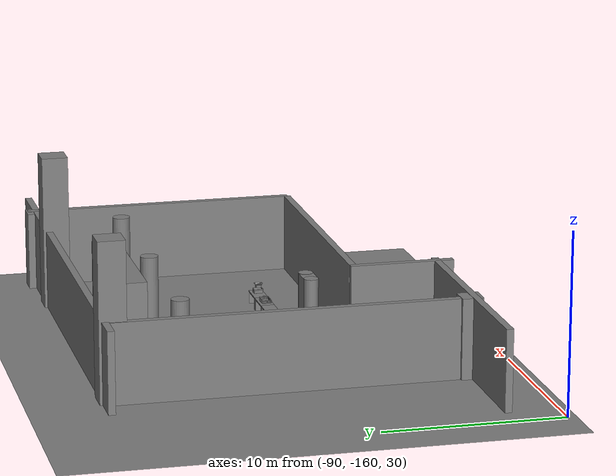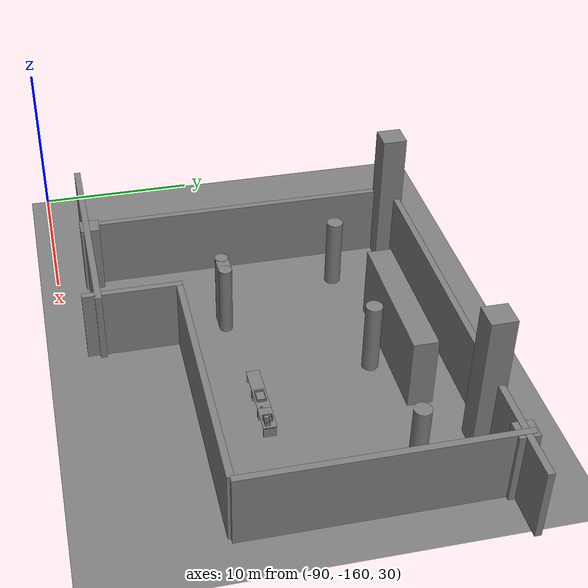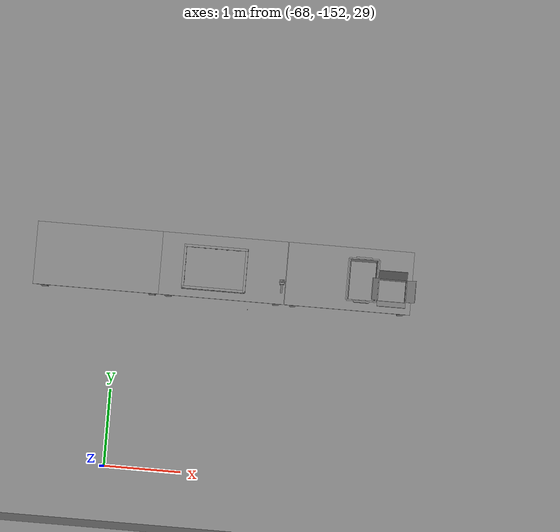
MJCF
<mujoco>
    <option gravity="0.000000000 0.000000000 -9.810000420" timestep="0.0049999999" integrator="implicitfast" density="1.225" viscosity="1.8000001e-05" noslip_iterations="10" iterations="100" sdf_iterations="50">
        <flag multiccd="disable"/>
    </option>
    <size memory="1000M"/>
    <compiler coordinate="local"/>
    <worldbody>
        <light cutoff="30" pos="0 1 1" dir="0 -1 -2"/>
        <light cutoff="30" pos="0 -1 1" dir="0 1 -2"/>
        <body pos="-64.866622925 -149.383972168 30.183746338" euler="89.999992371 89.999946594 0.000000000" name="openloong_gripper_2f85_fix_base_usda_bluebox_01">
            <geom contype="1" conaffinity="1" density="1000" type="box" material="" rgba="0.500000000 0.500000000 0.500000000 1.000000000" solimp="0.899999976 0.949999988 0.001000000" friction="1.000000000 0.005000000 0.000100000" solref="0.020000000 1.000000000" margin="0" condim="3" group="0" pos="0.276596069 0.187225342 0.000061035" quat="0.707107008 0.000077501 0.707106471 0.000077456" size="0.100000001 0.057999998 0.010000000" name="openloong_gripper_2f85_fix_base_usda_geom_4F6A55DF_0D54_45F4_99C2_096E6A0FEFEF"/>
            <geom contype="1" conaffinity="1" density="1000" type="box" material="" rgba="0.500000000 0.500000000 0.500000000 1.000000000" solimp="0.899999976 0.949999988 0.001000000" friction="1.000000000 0.005000000 0.000100000" solref="0.020000000 1.000000000" margin="0" condim="3" group="0" pos="0.000000000 0.002883911 0.000000000" quat="1.000000000 0.000000000 0.000000000 0.000000000" size="0.254000008 0.003000000 0.172000006" name="openloong_gripper_2f85_fix_base_usda_geom_5A7C494F_858D_49D2_BECD_F7E36E872E90"/>
            <geom contype="1" conaffinity="1" density="1000" type="box" material="" rgba="0.500000000 0.500000000 0.500000000 1.000000000" solimp="0.899999976 0.949999988 0.001000000" friction="1.000000000 0.005000000 0.000100000" solref="0.020000000 1.000000000" margin="0" condim="3" group="0" pos="0.000015259 0.124874115 0.173477173" quat="0.999796450 0.020176515 -0.000000015 0.000000030" size="0.259999990 0.119999997 0.007000000" name="openloong_gripper_2f85_fix_base_usda_geom_694BDAF3_7A12_4C07_8FE9_295E5BEA7BBA"/>
            <geom contype="1" conaffinity="1" density="1000" type="box" material="" rgba="0.500000000 0.500000000 0.500000000 1.000000000" solimp="0.899999976 0.949999988 0.001000000" friction="1.000000000 0.005000000 0.000100000" solref="0.020000000 1.000000000" margin="0" condim="3" group="0" pos="0.000015259 0.124874115 -0.173477173" quat="0.999796450 -0.020176545 -0.000000015 0.000000000" size="0.259999990 0.119999997 0.007000000" name="openloong_gripper_2f85_fix_base_usda_geom_64AE5E1A_377F_4050_A804_FE599D2CAC91"/>
            <geom contype="1" conaffinity="1" density="1000" type="box" material="" rgba="0.500000000 0.500000000 0.500000000 1.000000000" solimp="0.899999976 0.949999988 0.001000000" friction="1.000000000 0.005000000 0.000100000" solref="0.020000000 1.000000000" margin="0" condim="3" group="0" pos="0.000015259 0.214012146 0.188980103" quat="0.999913096 0.013176724 0.000000015 0.000000000" size="0.259999990 0.029999999 0.012500000" name="openloong_gripper_2f85_fix_base_usda_geom_D9466693_92B3_4811_B950_B6335F85DACB"/>
            <geom contype="1" conaffinity="1" density="1000" type="box" material="" rgba="0.500000000 0.500000000 0.500000000 1.000000000" solimp="0.899999976 0.949999988 0.001000000" friction="1.000000000 0.005000000 0.000100000" solref="0.020000000 1.000000000" margin="0" condim="3" group="0" pos="-0.258346558 0.125289917 0.001876831" quat="0.702796996 -0.020792052 0.710783184 0.020769238" size="0.189999998 0.119999997 0.009000000" name="openloong_gripper_2f85_fix_base_usda_geom_D92BAE63_07EB_4F61_AA94_7F99AD81E197"/>
            <geom contype="1" conaffinity="1" density="1000" type="box" material="" rgba="0.500000000 0.500000000 0.500000000 1.000000000" solimp="0.899999976 0.949999988 0.001000000" friction="1.000000000 0.005000000 0.000100000" solref="0.020000000 1.000000000" margin="0" condim="3" group="0" pos="0.000015259 0.214012146 -0.188980103" quat="0.999913096 -0.013176769 0.000000030 0.000000015" size="0.259999990 0.029999999 0.012500000" name="openloong_gripper_2f85_fix_base_usda_geom_06A3B9F2_133E_4627_AF2B_3A9369FD3549"/>
            <geom contype="1" conaffinity="1" density="1000" type="box" material="" rgba="0.500000000 0.500000000 0.500000000 1.000000000" solimp="0.899999976 0.949999988 0.001000000" friction="1.000000000 0.005000000 0.000100000" solref="0.020000000 1.000000000" margin="0" condim="3" group="0" pos="-0.276596069 0.187225342 0.000061035" quat="0.707106650 0.000077441 0.707106709 0.000077456" size="0.100000001 0.057999998 0.010000000" name="openloong_gripper_2f85_fix_base_usda_geom_789C727D_0069_4E7D_AFBE_A3C9BAB3336C"/>
            <geom contype="1" conaffinity="1" density="1000" type="box" material="" rgba="0.500000000 0.500000000 0.500000000 1.000000000" solimp="0.899999976 0.949999988 0.001000000" friction="1.000000000 0.005000000 0.000100000" solref="0.020000000 1.000000000" margin="0" condim="3" group="0" pos="0.258346558 0.125289917 0.001876831" quat="0.702851534 0.018856451 0.710823834 -0.019329429" size="0.189999998 0.119999997 0.009000000" name="openloong_gripper_2f85_fix_base_usda_geom_162663D5_0FE4_41CE_A6E3_D5035A0A6B5E"/>
            <freejoint name="openloong_gripper_2f85_fix_base_usda_bluebox_01_joint"/>
            <site size="0.005000000 0.005000000 0.005000000" rgba="0.500000000 0.500000000 0.500000000 1.000000000" pos="0.000000000 0.000000000 0.000000000" quat="0.999961913 0.008726534 0.000000000 0.000000000" group="0" type="sphere" name="openloong_gripper_2f85_fix_base_usda_bluebox_01site"/>
        </body>
        <body pos="-64.496299744 -149.491867065 30.235729218" euler="0.000000000 0.000000000 89.999946594" name="openloong_gripper_2f85_fix_base_usda_cardboardbox_01">
            <geom contype="1" conaffinity="1" density="1000" type="box" material="" rgba="0.500000000 0.500000000 0.500000000 1.000000000" solimp="0.899999976 0.949999988 0.001000000" friction="1.000000000 0.005000000 0.000100000" solref="0.020000000 1.000000000" margin="0" condim="3" group="0" pos="-0.003166199 -0.004086494 0.005052090" quat="1.000000000 0.000000000 0.000000000 0.000000000" size="0.142499998 0.177500010 0.005000000" name="openloong_gripper_2f85_fix_base_usda_geom_B303BDA7_0936_4AC2_880A_44DA362F2F17"/>
            <geom contype="1" conaffinity="1" density="1000" type="box" material="" rgba="0.500000000 0.500000000 0.500000000 1.000000000" solimp="0.899999976 0.949999988 0.001000000" friction="1.000000000 0.005000000 0.000100000" solref="0.020000000 1.000000000" margin="0" condim="3" group="0" pos="-0.003166199 0.170316696 0.150570869" quat="1.000000000 0.000000000 0.000000000 0.000000000" size="0.142499998 0.005000000 0.149999991" name="openloong_gripper_2f85_fix_base_usda_geom_2282ED6E_B92C_4756_A6F0_E1DC34E37102"/>
            <geom contype="1" conaffinity="1" density="1000" type="box" material="" rgba="0.500000000 0.500000000 0.500000000 1.000000000" solimp="0.899999976 0.949999988 0.001000000" friction="1.000000000 0.005000000 0.000100000" solref="0.020000000 1.000000000" margin="0" condim="3" group="0" pos="-0.147399902 -0.005307198 0.150570869" quat="1.000000000 0.000000000 0.000000000 0.000000000" size="0.005000000 0.177500010 0.149999991" name="openloong_gripper_2f85_fix_base_usda_geom_07CE5F07_A9A3_4A91_B433_2F13EBB5FE59"/>
            <geom contype="1" conaffinity="1" density="1000" type="box" material="" rgba="0.500000000 0.500000000 0.500000000 1.000000000" solimp="0.899999976 0.949999988 0.001000000" friction="1.000000000 0.005000000 0.000100000" solref="0.020000000 1.000000000" margin="0" condim="3" group="0" pos="0.140275955 -0.005307198 0.150570869" quat="1.000000000 0.000000000 0.000000000 0.000000000" size="0.005000000 0.177500010 0.149999991" name="openloong_gripper_2f85_fix_base_usda_geom_3C840E57_D46D_45E1_90C6_A893E478B4C3"/>
            <geom contype="1" conaffinity="1" density="1000" type="box" material="" rgba="0.500000000 0.500000000 0.500000000 1.000000000" solimp="0.899999976 0.949999988 0.001000000" friction="1.000000000 0.005000000 0.000100000" solref="0.020000000 1.000000000" margin="0" condim="3" group="0" pos="-0.003166199 -0.181550980 0.150570869" quat="1.000000000 0.000000000 0.000000000 0.000000000" size="0.142499998 0.005000000 0.149999991" name="openloong_gripper_2f85_fix_base_usda_geom_886D7425_94E7_475E_B184_C13A91B22104"/>
            <freejoint name="openloong_gripper_2f85_fix_base_usda_cardboardbox_01_joint"/>
            <site size="0.005000000 0.005000000 0.005000000" rgba="0.500000000 0.500000000 0.500000000 1.000000000" pos="0.000000000 0.000000000 0.000000000" quat="0.999961913 0.008726535 0.000000000 0.000000000" group="0" type="sphere" name="openloong_gripper_2f85_fix_base_usda_site_5A8361AF_E4DA_4CFC_B627_491325BC6B10"/>
            <body pos="0.139160156 -0.004048347 0.301930904" euler="-179.999954224 49.383502960 179.999954224" name="openloong_gripper_2f85_fix_base_usda_A1_006">
                <geom contype="1" conaffinity="1" density="1000" type="box" material="" rgba="0.500000000 0.500000000 0.500000000 1.000000000" solimp="0.899999976 0.949999988 0.001000000" friction="1.000000000 0.005000000 0.000100000" solref="0.020000000 1.000000000" margin="0" condim="3" group="0" pos="-0.071587563 0.000009537 0.001745224" quat="0.999999881 0.000000000 0.000000000 0.000000000" size="0.071249999 0.179999992 0.002500000" name="openloong_gripper_2f85_fix_base_usda_geom_842A35AA_A80C_4486_B5A4_EE4EEF25A965"/>
                <joint armature="0" stiffness="0.07" damping="0.0099999998" axis="0.000000 1.000000 0.000000" type="hinge" name="openloong_gripper_2f85_fix_base_usda_A1_006"/>
            </body>
            <body pos="-0.145902634 -0.004086494 0.301938057" euler="-180.000000000 -60.000011444 -180.000000000" name="openloong_gripper_2f85_fix_base_usda_A2_006">
                <geom contype="1" conaffinity="1" density="1000" type="box" material="" rgba="0.500000000 0.500000000 0.500000000 1.000000000" solimp="0.899999976 0.949999988 0.001000000" friction="1.000000000 0.005000000 0.000100000" solref="0.020000000 1.000000000" margin="0" condim="3" group="0" pos="0.071268082 0.000009537 0.002717972" quat="0.000002921 0.000000000 -0.000000030 0.999999881" size="0.071249999 0.179999992 0.002500000" name="openloong_gripper_2f85_fix_base_usda_geom_FD7AB0B9_D5E0_43C4_91C2_74D257E75EAF"/>
                <joint armature="0" stiffness="0.07" damping="0.0099999998" axis="0.000000 1.000000 0.000000" type="hinge" name="openloong_gripper_2f85_fix_base_usda_A2_006"/>
            </body>
            <body pos="-0.003385544 0.175991058 0.301930904" euler="-125.858116150 -0.000004561 0.000002331" name="openloong_gripper_2f85_fix_base_usda_B2_006">
                <geom contype="1" conaffinity="1" density="1000" type="box" material="" rgba="0.500000000 0.500000000 0.500000000 1.000000000" solimp="0.899999976 0.949999988 0.001000000" friction="1.000000000 0.005000000 0.000100000" solref="0.020000000 1.000000000" margin="0" condim="3" group="0" pos="0.000009537 -0.070939064 -0.002470016" quat="0.999614120 0.027776197 -0.000000015 0.000000030" size="0.137500003 0.064999998 0.005000000" name="openloong_gripper_2f85_fix_base_usda_geom_8F6E8ADF_C478_48CE_8275_3BE85546BE9B"/>
                <joint armature="0" stiffness="0.07" damping="0.0099999998" axis="1.000000 0.000000 0.000000" type="hinge" name="openloong_gripper_2f85_fix_base_usda_B2_006"/>
            </body>
            <body pos="-0.003385544 -0.184140205 0.301938057" euler="147.805557251 0.000000000 0.000000000" name="openloong_gripper_2f85_fix_base_usda_B1_006">
                <geom contype="1" conaffinity="1" density="1000" type="box" material="" rgba="0.500000000 0.500000000 0.500000000 1.000000000" solimp="0.899999976 0.949999988 0.001000000" friction="1.000000000 0.005000000 0.000100000" solref="0.020000000 1.000000000" margin="0" condim="3" group="0" pos="-0.000028610 0.070202351 -0.002703667" quat="0.999614179 -0.027776167 0.000000000 0.000000000" size="0.137500003 0.064999998 0.005000000" name="openloong_gripper_2f85_fix_base_usda_geom_A6A23B00_5B32_4EE5_9C90_1C5E916FEE20"/>
                <joint armature="0" stiffness="0.07" damping="0.0099999998" axis="1.000000 0.000000 0.000000" type="hinge" name="openloong_gripper_2f85_fix_base_usda_B1_006"/>
            </body>
        </body>
        <body pos="-65.882858276 -149.481979370 30.229999542" euler="-64.487716675 0.000000000 0.000000000" name="openloong_gripper_2f85_fix_base_usda_Barcode">
            <geom contype="1" conaffinity="1" density="1000" type="box" material="" rgba="0.500000000 0.500000000 0.500000000 1.000000000" solimp="0.899999976 0.949999988 0.001000000" friction="1.000000000 0.005000000 0.000100000" solref="0.020000000 1.000000000" margin="0" condim="3" group="0" pos="0.000000000 0.013038635 0.001419067" quat="0.000000000 0.000000000 0.000000000 1.000000119" size="0.034000002 0.010000000 0.017999999" name="openloong_gripper_2f85_fix_base_usda_geom_F5D32B8F_7664_4D29_B022_B0B974FEDF0C"/>
            <geom contype="1" conaffinity="1" density="1000" type="box" material="" rgba="0.500000000 0.500000000 0.500000000 1.000000000" solimp="0.899999976 0.949999988 0.001000000" friction="1.000000000 0.005000000 0.000100000" solref="0.020000000 1.000000000" margin="0" condim="3" group="0" pos="0.000000000 -0.035301208 -0.007095337" quat="0.000000000 0.000000000 -0.043619365 0.999048233" size="0.028999999 0.010000000 0.020000000" name="openloong_gripper_2f85_fix_base_usda_geom_CF2233F0_23EB_4694_9904_ADA94910B1D2"/>
            <geom contype="1" conaffinity="1" density="1000" type="box" material="" rgba="0.500000000 0.500000000 0.500000000 1.000000000" solimp="0.899999976 0.949999988 0.001000000" friction="1.000000000 0.005000000 0.000100000" solref="0.020000000 1.000000000" margin="0" condim="3" group="0" pos="0.000000000 -0.043411255 -0.011749268" quat="0.922262907 0.386563420 0.000000000 0.000000000" size="0.026000001 0.010000000 0.020000000" name="openloong_gripper_2f85_fix_base_usda_geom_6A478ED3_81AA_45A1_BF62_3EE0ADF16866"/>
            <geom contype="1" conaffinity="1" density="1000" type="box" material="" rgba="0.500000000 0.500000000 0.500000000 1.000000000" solimp="0.899999976 0.949999988 0.001000000" friction="1.000000000 0.005000000 0.000100000" solref="0.020000000 1.000000000" margin="0" condim="3" group="0" pos="0.000000000 -0.016967773 -0.031860352" quat="0.000000000 0.000000000 0.000000000 1.000000119" size="0.008000000 0.010000000 0.013000000" name="openloong_gripper_2f85_fix_base_usda_geom_A74964FE_EBD8_4CAB_B8E2_05719182C0CD"/>
            <geom contype="1" conaffinity="1" density="1000" type="box" material="" rgba="0.500000000 0.500000000 0.500000000 1.000000000" solimp="0.899999976 0.949999988 0.001000000" friction="1.000000000 0.005000000 0.000100000" solref="0.020000000 1.000000000" margin="0" condim="3" group="0" pos="0.000000000 -0.001869202 0.000312805" quat="0.953716993 0.300705761 0.000000000 0.000000000" size="0.032000002 0.010000000 0.018999999" name="openloong_gripper_2f85_fix_base_usda_geom_AC235C30_A23F_4495_86DA_96B85FCED6EC"/>
            <geom contype="1" conaffinity="1" density="1000" type="box" material="" rgba="0.500000000 0.500000000 0.500000000 1.000000000" solimp="0.899999976 0.949999988 0.001000000" friction="1.000000000 0.005000000 0.000100000" solref="0.020000000 1.000000000" margin="0" condim="3" group="0" pos="0.000000000 -0.019531250 -0.003173828" quat="0.953716993 0.300705761 0.000000000 0.000000000" size="0.030999999 0.010000000 0.020000000" name="openloong_gripper_2f85_fix_base_usda_geom_254BECE5_E7AB_45C3_8789_47096562E862"/>
            <geom contype="1" conaffinity="1" density="1000" type="box" material="" rgba="0.500000000 0.500000000 0.500000000 1.000000000" solimp="0.899999976 0.949999988 0.001000000" friction="1.000000000 0.005000000 0.000100000" solref="0.020000000 1.000000000" margin="0" condim="3" group="0" pos="0.000000000 -0.035301208 -0.007095337" quat="0.953716993 0.300705761 0.000000000 0.000000000" size="0.028999999 0.010000000 0.020000000" name="openloong_gripper_2f85_fix_base_usda_geom_5999FBA7_8D02_43DA_8263_FF7FF819C074"/>
            <geom contype="1" conaffinity="1" density="1000" type="box" material="" rgba="0.500000000 0.500000000 0.500000000 1.000000000" solimp="0.899999976 0.949999988 0.001000000" friction="1.000000000 0.005000000 0.000100000" solref="0.020000000 1.000000000" margin="0" condim="3" group="0" pos="0.000000000 -0.042617798 -0.071121216" quat="0.000000000 0.000000000 0.000000000 1.000000119" size="0.013000000 0.021000000 0.059999999" name="openloong_gripper_2f85_fix_base_usda_geom_C22EF0EE_4E27_4C23_B9AD_FE69FCA1C713"/>
            <freejoint name="openloong_gripper_2f85_fix_base_usda_Barcode_joint"/>
            <site size="0.005000000 0.005000000 0.005000000" rgba="0.500000000 0.500000000 0.500000000 1.000000000" pos="0.000000000 0.000000000 0.000000000" quat="1.000000000 0.000000000 0.000000000 0.000000000" group="0" type="sphere" name="openloong_gripper_2f85_fix_base_usda_Barcode_site"/>
        </body>
        <body pos="-66.745018005 -149.392349243 30.184000015" euler="0.000000000 0.000000000 89.999946594" name="[22332662897789]_Basket_01">
            <geom contype="1" conaffinity="1" density="1000" type="box" material="" rgba="0.500000000 0.500000000 0.500000000 1.000000000" solimp="0.899999976 0.949999988 0.001000000" friction="1.000000000 0.005000000 0.000100000" solref="0.020000000 1.000000000" margin="0" condim="3" group="0" pos="-0.052425385 0.389207840 0.089787483" quat="0.707107008 0.000000000 0.000000000 0.707106411" size="0.014249999 0.014249999 0.059999999" name="[22332662897789]_geom_3B059D5C_2F49_4C72_9F1C_C722D3583A65"/>
            <geom contype="1" conaffinity="1" density="1000" type="box" material="" rgba="0.500000000 0.500000000 0.500000000 1.000000000" solimp="0.899999976 0.949999988 0.001000000" friction="1.000000000 0.005000000 0.000100000" solref="0.020000000 1.000000000" margin="0" condim="3" group="0" pos="0.264015198 -0.133043289 0.089787483" quat="0.707107008 0.000000000 0.000000000 0.707106411" size="0.014249999 0.014249999 0.059999999" name="[22332662897789]_geom_FEBADDE9_EA12_446D_9E5E_AB3E297A1F18"/>
            <geom contype="1" conaffinity="1" density="1000" type="box" material="" rgba="0.500000000 0.500000000 0.500000000 1.000000000" solimp="0.899999976 0.949999988 0.001000000" friction="1.000000000 0.005000000 0.000100000" solref="0.020000000 1.000000000" margin="0" condim="3" group="0" pos="-0.264015198 -0.265548706 0.089793205" quat="0.707107008 0.000000000 0.000000000 0.707106411" size="0.014249999 0.014249999 0.059999999" name="[22332662897789]_geom_E4DEDBC6_E905_480F_A1E3_2776DAF9256C"/>
            <geom contype="1" conaffinity="1" density="1000" type="box" material="" rgba="0.500000000 0.500000000 0.500000000 1.000000000" solimp="0.899999976 0.949999988 0.001000000" friction="1.000000000 0.005000000 0.000100000" solref="0.020000000 1.000000000" margin="0" condim="3" group="0" pos="-0.160263062 -0.389322281 0.089793205" quat="0.707107008 0.000000000 0.000000000 0.707106411" size="0.014249999 0.014249999 0.059999999" name="[22332662897789]_geom_DCF822A4_B275_43F8_BD76_AAB478C83324"/>
            <geom contype="1" conaffinity="1" density="1000" type="box" material="" rgba="0.500000000 0.500000000 0.500000000 1.000000000" solimp="0.899999976 0.949999988 0.001000000" friction="1.000000000 0.005000000 0.000100000" solref="0.020000000 1.000000000" margin="0" condim="3" group="0" pos="0.162265778 -0.389322281 0.089787483" quat="0.707107008 0.000000000 0.000000000 0.707106411" size="0.014249999 0.014249999 0.059999999" name="[22332662897789]_geom_347BDE39_C79C_4F91_9891_F82B59B9F425"/>
            <geom contype="1" conaffinity="1" density="1000" type="box" material="" rgba="0.500000000 0.500000000 0.500000000 1.000000000" solimp="0.899999976 0.949999988 0.001000000" friction="1.000000000 0.005000000 0.000100000" solref="0.020000000 1.000000000" margin="0" condim="3" group="0" pos="0.264015198 0.389207840 0.089787483" quat="0.707107008 0.000000000 0.000000000 0.707106411" size="0.014249999 0.014249999 0.059999999" name="[22332662897789]_geom_1D130A18_0E32_4736_9BDF_69DF14C50C93"/>
            <geom contype="1" conaffinity="1" density="1000" type="box" material="" rgba="0.500000000 0.500000000 0.500000000 1.000000000" solimp="0.899999976 0.949999988 0.001000000" friction="1.000000000 0.005000000 0.000100000" solref="0.020000000 1.000000000" margin="0" condim="3" group="0" pos="-0.264015198 -0.133043289 0.089793205" quat="0.707107008 0.000000000 0.000000000 0.707106411" size="0.014249999 0.014249999 0.059999999" name="[22332662897789]_geom_9DE7452D_6D75_4F8A_949F_C0C280119E41"/>
            <geom contype="1" conaffinity="1" density="1000" type="box" material="" rgba="0.500000000 0.500000000 0.500000000 1.000000000" solimp="0.899999976 0.949999988 0.001000000" friction="1.000000000 0.005000000 0.000100000" solref="0.020000000 1.000000000" margin="0" condim="3" group="0" pos="-0.264026642 0.269256592 0.089793205" quat="0.707107008 0.000000000 0.000000000 0.707106411" size="0.014249999 0.014249999 0.059999999" name="[22332662897789]_geom_F660FC87_5F30_470E_B99E_9103A73DFD5E"/>
            <geom contype="1" conaffinity="1" density="1000" type="box" material="" rgba="0.500000000 0.500000000 0.500000000 1.000000000" solimp="0.899999976 0.949999988 0.001000000" friction="1.000000000 0.005000000 0.000100000" solref="0.020000000 1.000000000" margin="0" condim="3" group="0" pos="0.054462433 0.389207840 0.089787483" quat="0.707107008 0.000000000 0.000000000 0.707106411" size="0.014249999 0.014249999 0.059999999" name="[22332662897789]_geom_5A2D61FF_A12B_45E8_944D_1573AF606488"/>
            <geom contype="1" conaffinity="1" density="1000" type="box" material="" rgba="0.500000000 0.500000000 0.500000000 1.000000000" solimp="0.899999976 0.949999988 0.001000000" friction="1.000000000 0.005000000 0.000100000" solref="0.020000000 1.000000000" margin="0" condim="3" group="0" pos="0.054462433 -0.389322281 0.089787483" quat="0.707107008 0.000000000 0.000000000 0.707106411" size="0.014249999 0.014249999 0.059999999" name="[22332662897789]_geom_B8831FC9_9FE3_4D74_BF3C_F42CD0576A28"/>
            <geom contype="1" conaffinity="1" density="1000" type="box" material="" rgba="0.500000000 0.500000000 0.500000000 1.000000000" solimp="0.899999976 0.949999988 0.001000000" friction="1.000000000 0.005000000 0.000100000" solref="0.020000000 1.000000000" margin="0" condim="3" group="0" pos="0.264015198 0.269256592 0.089793205" quat="0.707107008 0.000000000 0.000000000 0.707106411" size="0.014249999 0.014249999 0.059999999" name="[22332662897789]_geom_82EE4BC6_DF39_4C97_812F_DA35D3DB066D"/>
            <geom contype="1" conaffinity="1" density="1000" type="box" material="" rgba="0.500000000 0.500000000 0.500000000 1.000000000" solimp="0.899999976 0.949999988 0.001000000" friction="1.000000000 0.005000000 0.000100000" solref="0.020000000 1.000000000" margin="0" condim="3" group="0" pos="0.264015198 -0.389322281 0.089787483" quat="0.707107008 0.000000000 0.000000000 0.707106411" size="0.014249999 0.014249999 0.059999999" name="[22332662897789]_geom_206840CF_72B9_44E7_90E7_9CD4517E7963"/>
            <geom contype="1" conaffinity="1" density="1000" type="box" material="" rgba="0.500000000 0.500000000 0.500000000 1.000000000" solimp="0.899999976 0.949999988 0.001000000" friction="1.000000000 0.005000000 0.000100000" solref="0.020000000 1.000000000" margin="0" condim="3" group="0" pos="0.000000000 0.000000000 0.015998840" quat="0.707107008 0.000000000 0.000000000 0.707106411" size="0.403499991 0.279000014 0.015750000" name="[22332662897789]_geom_6854C24C_C6A8_4B99_A6EC_A34E7919990D"/>
            <geom contype="1" conaffinity="1" density="1000" type="box" material="" rgba="0.500000000 0.500000000 0.500000000 1.000000000" solimp="0.899999976 0.949999988 0.001000000" friction="1.000000000 0.005000000 0.000100000" solref="0.020000000 1.000000000" margin="0" condim="3" group="0" pos="0.000000000 -0.389476776 0.163619041" quat="0.707107008 0.000000000 0.000000000 0.707106411" size="0.015000000 0.277500004 0.015750000" name="[22332662897789]_geom_3ADADAE6_288B_49EF_AB4A_E6EE6B8221ED"/>
            <geom contype="1" conaffinity="1" density="1000" type="box" material="" rgba="0.500000000 0.500000000 0.500000000 1.000000000" solimp="0.899999976 0.949999988 0.001000000" friction="1.000000000 0.005000000 0.000100000" solref="0.020000000 1.000000000" margin="0" condim="3" group="0" pos="0.162265778 0.389207840 0.089787483" quat="0.707107008 0.000000000 0.000000000 0.707106411" size="0.014249999 0.014249999 0.059999999" name="[22332662897789]_geom_28307740_4700_47DC_88D0_B86B4A1CE964"/>
            <geom contype="1" conaffinity="1" density="1000" type="box" material="" rgba="0.500000000 0.500000000 0.500000000 1.000000000" solimp="0.899999976 0.949999988 0.001000000" friction="1.000000000 0.005000000 0.000100000" solref="0.020000000 1.000000000" margin="0" condim="3" group="0" pos="0.000000000 0.389471054 0.163619041" quat="0.707107008 0.000000000 0.000000000 0.707106411" size="0.015000000 0.277500004 0.015750000" name="[22332662897789]_geom_49D714F1_B826_438C_8C3D_240852372BA3"/>
            <geom contype="1" conaffinity="1" density="1000" type="box" material="" rgba="0.500000000 0.500000000 0.500000000 1.000000000" solimp="0.899999976 0.949999988 0.001000000" friction="1.000000000 0.005000000 0.000100000" solref="0.020000000 1.000000000" margin="0" condim="3" group="0" pos="-0.263511658 0.000000000 0.163619041" quat="0.707107008 0.000000000 0.000000000 0.707106411" size="0.403499991 0.015000000 0.015750000" name="[22332662897789]_geom_42445C32_AE72_4FB4_9C5C_F8914FEB7BB0"/>
            <geom contype="1" conaffinity="1" density="1000" type="box" material="" rgba="0.500000000 0.500000000 0.500000000 1.000000000" solimp="0.899999976 0.949999988 0.001000000" friction="1.000000000 0.005000000 0.000100000" solref="0.020000000 1.000000000" margin="0" condim="3" group="0" pos="-0.264015198 0.141334534 0.089793205" quat="0.707107008 0.000000000 0.000000000 0.707106411" size="0.014249999 0.014249999 0.059999999" name="[22332662897789]_geom_A3483ABD_96DF_4A92_B833_E4F33DC68E96"/>
            <geom contype="1" conaffinity="1" density="1000" type="box" material="" rgba="0.500000000 0.500000000 0.500000000 1.000000000" solimp="0.899999976 0.949999988 0.001000000" friction="1.000000000 0.005000000 0.000100000" solref="0.020000000 1.000000000" margin="0" condim="3" group="0" pos="0.264015198 -0.265548706 0.089787483" quat="0.707107008 0.000000000 0.000000000 0.707106411" size="0.014249999 0.014249999 0.059999999" name="[22332662897789]_geom_B23BAAC2_4A12_4F67_93B9_F3774097F7D0"/>
            <geom contype="1" conaffinity="1" density="1000" type="box" material="" rgba="0.500000000 0.500000000 0.500000000 1.000000000" solimp="0.899999976 0.949999988 0.001000000" friction="1.000000000 0.005000000 0.000100000" solref="0.020000000 1.000000000" margin="0" condim="3" group="0" pos="-0.160263062 0.389207840 0.089787483" quat="0.707107008 0.000000000 0.000000000 0.707106411" size="0.014249999 0.014249999 0.059999999" name="[22332662897789]_geom_2C496A6D_0C00_436F_92C8_6227A504086F"/>
            <geom contype="1" conaffinity="1" density="1000" type="box" material="" rgba="0.500000000 0.500000000 0.500000000 1.000000000" solimp="0.899999976 0.949999988 0.001000000" friction="1.000000000 0.005000000 0.000100000" solref="0.020000000 1.000000000" margin="0" condim="3" group="0" pos="-0.052425385 -0.389322281 0.089787483" quat="0.707107008 0.000000000 0.000000000 0.707106411" size="0.014249999 0.014249999 0.059999999" name="[22332662897789]_geom_92308724_43F4_4982_AA8F_7C54929B0000"/>
            <geom contype="1" conaffinity="1" density="1000" type="box" material="" rgba="0.500000000 0.500000000 0.500000000 1.000000000" solimp="0.899999976 0.949999988 0.001000000" friction="1.000000000 0.005000000 0.000100000" solref="0.020000000 1.000000000" margin="0" condim="3" group="0" pos="-0.264026642 -0.389322281 0.089793205" quat="0.707107008 0.000000000 0.000000000 0.707106411" size="0.014249999 0.014249999 0.059999999" name="[22332662897789]_geom_6DAD81EC_D77E_4FE8_A6C1_25E14FD2CD52"/>
            <geom contype="1" conaffinity="1" density="1000" type="box" material="" rgba="0.500000000 0.500000000 0.500000000 1.000000000" solimp="0.899999976 0.949999988 0.001000000" friction="1.000000000 0.005000000 0.000100000" solref="0.020000000 1.000000000" margin="0" condim="3" group="0" pos="0.264015198 0.141334534 0.089787483" quat="0.707107008 0.000000000 0.000000000 0.707106411" size="0.014249999 0.014249999 0.059999999" name="[22332662897789]_geom_E88EA533_0297_48BF_93D1_136703C8A98A"/>
            <geom contype="1" conaffinity="1" density="1000" type="box" material="" rgba="0.500000000 0.500000000 0.500000000 1.000000000" solimp="0.899999976 0.949999988 0.001000000" friction="1.000000000 0.005000000 0.000100000" solref="0.020000000 1.000000000" margin="0" condim="3" group="0" pos="-0.264015198 0.389207840 0.089793205" quat="0.707107008 0.000000000 0.000000000 0.707106411" size="0.014249999 0.014249999 0.059999999" name="[22332662897789]_geom_9B16E255_CB80_47E5_A7D9_F9A3748E1FDF"/>
            <geom contype="1" conaffinity="1" density="1000" type="box" material="" rgba="0.500000000 0.500000000 0.500000000 1.000000000" solimp="0.899999976 0.949999988 0.001000000" friction="1.000000000 0.005000000 0.000100000" solref="0.020000000 1.000000000" margin="0" condim="3" group="0" pos="0.264015198 0.004480362 0.089787483" quat="0.707107008 0.000000000 0.000000000 0.707106411" size="0.014249999 0.014249999 0.059999999" name="[22332662897789]_geom_588A43C4_8691_44DC_986A_5E7D5F71FED4"/>
            <geom contype="1" conaffinity="1" density="1000" type="box" material="" rgba="0.500000000 0.500000000 0.500000000 1.000000000" solimp="0.899999976 0.949999988 0.001000000" friction="1.000000000 0.005000000 0.000100000" solref="0.020000000 1.000000000" margin="0" condim="3" group="0" pos="0.263694763 -0.000011444 0.163619041" quat="0.707107008 0.000000000 0.000000000 0.707106411" size="0.403499991 0.015000000 0.015750000" name="[22332662897789]_geom_DC7DE05A_0424_4DF9_B799_CD0A88A57B4A"/>
            <geom contype="1" conaffinity="1" density="1000" type="box" material="" rgba="0.500000000 0.500000000 0.500000000 1.000000000" solimp="0.899999976 0.949999988 0.001000000" friction="1.000000000 0.005000000 0.000100000" solref="0.020000000 1.000000000" margin="0" condim="3" group="0" pos="-0.264015198 0.004480362 0.089793205" quat="0.707107008 0.000000000 0.000000000 0.707106411" size="0.014249999 0.014249999 0.059999999" name="[22332662897789]_geom_DE2B29B6_BFFD_4A3C_897C_57A74738092B"/>
            <freejoint name="[22332662897789]_joint_2B6EE2A2_8235_4FEE_9C94_B761EA36F4B2"/>
        </body>
        <body pos="0.000000000 0.000000000 0.000000000" euler="0.000000000 0.000000000 0.000000000" name="Static Objects_Static Objects">
            <geom contype="1" conaffinity="1" density="1000" type="box" material="" rgba="0.500000000 0.500000000 0.500000000 1.000000000" solimp="0.899999976 0.949999988 0.001000000" friction="1.000000000 0.005000000 0.000100000" solref="0.020000000 1.000000000" margin="0" condim="3" group="0" pos="-67.544113159 -149.365814209 29.727830887" quat="0.500000417 0.499999970 0.499999553 0.499999970" size="0.381000012 0.319999993 0.041000001" name="Static Objects_geom_B99955FA_29AB_4B71_94C9_E01B7909D58A"/>
            <geom contype="1" conaffinity="1" density="1000" type="box" material="" rgba="0.500000000 0.500000000 0.500000000 1.000000000" solimp="0.899999976 0.949999988 0.001000000" friction="1.000000000 0.005000000 0.000100000" solref="0.020000000 1.000000000" margin="0" condim="3" group="0" pos="-68.239501953 -149.365814209 30.086868286" quat="0.500000417 0.499999970 0.499999553 0.499999970" size="0.370999992 0.039500002 0.745000005" name="Static Objects_geom_118C2629_41A5_4BA7_B1FA_A3AD5EA9275C"/>
            <geom contype="1" conaffinity="1" density="1000" type="box" material="" rgba="0.500000000 0.500000000 0.500000000 1.000000000" solimp="0.899999976 0.949999988 0.001000000" friction="1.000000000 0.005000000 0.000100000" solref="0.020000000 1.000000000" margin="0" condim="3" group="0" pos="-68.239501953 -149.365814209 30.147235870" quat="0.500000417 0.499999970 0.499999553 0.499999970" size="0.400000006 0.022000000 0.800000012" name="Static Objects_geom_76FA2248_12FC_4E7F_A5A6_DA68F7FD39D7"/>
            <geom contype="1" conaffinity="1" density="1000" type="box" material="" rgba="0.500000000 0.500000000 0.500000000 1.000000000" solimp="0.899999976 0.949999988 0.001000000" friction="1.000000000 0.005000000 0.000100000" solref="0.020000000 1.000000000" margin="0" condim="3" group="0" pos="-68.934890747 -149.365814209 29.727830887" quat="0.500000417 0.499999970 0.499999553 0.499999970" size="0.381000012 0.319999993 0.041000001" name="Static Objects_geom_AF044F4E_3BA6_4BD7_86FC_807EAE5381D4"/>
            <geom contype="1" conaffinity="1" density="1000" type="box" material="" rgba="0.500000000 0.500000000 0.500000000 1.000000000" solimp="0.899999976 0.949999988 0.001000000" friction="1.000000000 0.005000000 0.000100000" solref="0.020000000 1.000000000" margin="0" condim="3" group="0" pos="-68.239501953 -149.365814209 29.561563492" quat="0.500000417 0.499999970 0.499999553 0.499999970" size="0.020000000 0.022000000 0.660000026" name="Static Objects_geom_61EB932A_5A2B_48B2_B99D_64CA3A8E333C"/>
            <geom contype="1" conaffinity="1" density="1000" type="box" material="" rgba="0.500000000 0.500000000 0.500000000 1.000000000" solimp="0.899999976 0.949999988 0.001000000" friction="1.000000000 0.005000000 0.000100000" solref="0.020000000 1.000000000" margin="0" condim="3" group="0" pos="-65.945671082 -149.365814209 29.727830887" quat="0.500000417 0.499999970 0.499999553 0.499999970" size="0.381000012 0.319999993 0.041000001" name="Static Objects_geom_4D41A193_7642_4683_A831_9BD1390888D8"/>
            <geom contype="1" conaffinity="1" density="1000" type="box" material="" rgba="0.500000000 0.500000000 0.500000000 1.000000000" solimp="0.899999976 0.949999988 0.001000000" friction="1.000000000 0.005000000 0.000100000" solref="0.020000000 1.000000000" margin="0" condim="3" group="0" pos="-66.641059875 -149.365814209 30.086868286" quat="0.500000417 0.499999970 0.499999553 0.499999970" size="0.370999992 0.039500002 0.745000005" name="Static Objects_geom_CA03B1CE_1459_497F_90D7_EC177DF84139"/>
            <geom contype="1" conaffinity="1" density="1000" type="box" material="" rgba="0.500000000 0.500000000 0.500000000 1.000000000" solimp="0.899999976 0.949999988 0.001000000" friction="1.000000000 0.005000000 0.000100000" solref="0.020000000 1.000000000" margin="0" condim="3" group="0" pos="-66.641059875 -149.365814209 30.147235870" quat="0.500000417 0.499999970 0.499999553 0.499999970" size="0.400000006 0.022000000 0.800000012" name="Static Objects_geom_BA31846C_6AED_4B38_80F2_1A6D3DDBF2DB"/>
            <geom contype="1" conaffinity="1" density="1000" type="box" material="" rgba="0.500000000 0.500000000 0.500000000 1.000000000" solimp="0.899999976 0.949999988 0.001000000" friction="1.000000000 0.005000000 0.000100000" solref="0.020000000 1.000000000" margin="0" condim="3" group="0" pos="-67.336448669 -149.365814209 29.727830887" quat="0.500000417 0.499999970 0.499999553 0.499999970" size="0.381000012 0.319999993 0.041000001" name="Static Objects_geom_15492DCB_4674_4559_9126_F4AB1442BAD7"/>
            <geom contype="1" conaffinity="1" density="1000" type="box" material="" rgba="0.500000000 0.500000000 0.500000000 1.000000000" solimp="0.899999976 0.949999988 0.001000000" friction="1.000000000 0.005000000 0.000100000" solref="0.020000000 1.000000000" margin="0" condim="3" group="0" pos="-66.641059875 -149.365814209 29.561563492" quat="0.500000417 0.499999970 0.499999553 0.499999970" size="0.020000000 0.022000000 0.660000026" name="Static Objects_geom_03D1E7DF_433B_4086_A96D_026C8906C233"/>
            <geom contype="1" conaffinity="1" density="1000" type="box" material="" rgba="0.500000000 0.500000000 0.500000000 1.000000000" solimp="0.899999976 0.949999988 0.001000000" friction="1.000000000 0.005000000 0.000100000" solref="0.020000000 1.000000000" margin="0" condim="3" group="0" pos="-64.338577271 -149.365814209 29.727830887" quat="0.500000417 0.499999970 0.499999553 0.499999970" size="0.381000012 0.319999993 0.041000001" name="Static Objects_geom_5F1A794E_D5F1_4612_A0E4_B33107A6F76F"/>
            <geom contype="1" conaffinity="1" density="1000" type="box" material="" rgba="0.500000000 0.500000000 0.500000000 1.000000000" solimp="0.899999976 0.949999988 0.001000000" friction="1.000000000 0.005000000 0.000100000" solref="0.020000000 1.000000000" margin="0" condim="3" group="0" pos="-65.033966064 -149.365814209 30.086868286" quat="0.500000417 0.499999970 0.499999553 0.499999970" size="0.370999992 0.039500002 0.745000005" name="Static Objects_geom_6EC1A39D_0051_41CF_92DC_8DBC9ED586FD"/>
            <geom contype="1" conaffinity="1" density="1000" type="box" material="" rgba="0.500000000 0.500000000 0.500000000 1.000000000" solimp="0.899999976 0.949999988 0.001000000" friction="1.000000000 0.005000000 0.000100000" solref="0.020000000 1.000000000" margin="0" condim="3" group="0" pos="-65.033966064 -149.365814209 30.147235870" quat="0.500000417 0.499999970 0.499999553 0.499999970" size="0.400000006 0.022000000 0.800000012" name="Static Objects_geom_CD0F6F61_B7C2_44B1_A57B_DF4F58411504"/>
            <geom contype="1" conaffinity="1" density="1000" type="box" material="" rgba="0.500000000 0.500000000 0.500000000 1.000000000" solimp="0.899999976 0.949999988 0.001000000" friction="1.000000000 0.005000000 0.000100000" solref="0.020000000 1.000000000" margin="0" condim="3" group="0" pos="-65.729354858 -149.365814209 29.727830887" quat="0.500000417 0.499999970 0.499999553 0.499999970" size="0.381000012 0.319999993 0.041000001" name="Static Objects_geom_7A60CC4F_7597_4276_9DE6_2E5EE60AED55"/>
            <geom contype="1" conaffinity="1" density="1000" type="box" material="" rgba="0.500000000 0.500000000 0.500000000 1.000000000" solimp="0.899999976 0.949999988 0.001000000" friction="1.000000000 0.005000000 0.000100000" solref="0.020000000 1.000000000" margin="0" condim="3" group="0" pos="-65.033966064 -149.365814209 29.561563492" quat="0.500000417 0.499999970 0.499999553 0.499999970" size="0.020000000 0.022000000 0.660000026" name="Static Objects_geom_4273F725_A7B2_42C4_A08A_BFB1A357253C"/>
            <geom contype="1" conaffinity="1" density="1000" type="box" material="" rgba="0.500000000 0.500000000 0.500000000 1.000000000" solimp="0.899999976 0.949999988 0.001000000" friction="1.000000000 0.005000000 0.000100000" solref="0.020000000 1.000000000" margin="0" condim="3" group="0" pos="-61.754566193 -137.853729248 33.906845093" quat="0.707107067 0.000000000 0.000000000 0.707106471" size="0.759999990 0.759999990 4.500000000" name="Static Objects_geom_06420833_98EA_4A8B_85AD_272EA4636DEE"/>
            <geom contype="1" conaffinity="1" density="1000" type="box" material="" rgba="0.500000000 0.500000000 0.500000000 1.000000000" solimp="0.899999976 0.949999988 0.001000000" friction="1.000000000 0.005000000 0.000100000" solref="0.020000000 1.000000000" margin="0" condim="3" group="0" pos="-57.511135101 -144.927108765 31.707921982" quat="1.000000000 0.000000000 0.000000000 0.000000000" size="0.200000003 8.000000000 2.299999952" name="Static Objects_geom_90AB9AA3_A1D6_4605_B302_7DAE6EDE0CEC"/>
            <geom contype="1" conaffinity="1" density="1000" type="box" material="" rgba="0.500000000 0.500000000 0.500000000 1.000000000" solimp="0.899999976 0.949999988 0.001000000" friction="1.000000000 0.005000000 0.000100000" solref="0.020000000 1.000000000" margin="0" condim="3" group="0" pos="-80.517646790 -157.574050903 31.688196182" quat="0.707107067 0.000000000 0.000000000 0.707106471" size="0.600000024 0.600000024 2.299999952" name="Static Objects_geom_DE863575_8F1D_4B4D_87AE_CF1184F6769C"/>
            <geom contype="1" conaffinity="1" density="1000" type="box" material="" rgba="0.500000000 0.500000000 0.500000000 1.000000000" solimp="0.899999976 0.949999988 0.001000000" friction="1.000000000 0.005000000 0.000100000" solref="0.020000000 1.000000000" margin="0" condim="3" group="0" pos="-80.711044312 -147.414932251 31.666158676" quat="1.000000000 0.000000000 0.000000000 0.000000000" size="0.200000003 10.000000000 2.299999952" name="Static Objects_geom_9753E175_E1C7_489B_BCA8_C10ED5D0C275"/>
            <geom contype="1" conaffinity="1" density="1000" type="box" material="" rgba="0.500000000 0.500000000 0.500000000 1.000000000" solimp="0.899999976 0.949999988 0.001000000" friction="1.000000000 0.005000000 0.000100000" solref="0.020000000 1.000000000" margin="0" condim="3" group="0" pos="-57.687217712 -137.434692383 31.688196182" quat="0.707107067 0.000000000 0.000000000 0.707106471" size="0.600000024 0.600000024 2.299999952" name="Static Objects_geom_70DFF9BB_A512_4ABA_8888_CC7C576F643B"/>
            <geom contype="1" conaffinity="1" density="1000" type="box" material="" rgba="0.500000000 0.500000000 0.500000000 1.000000000" solimp="0.899999976 0.949999988 0.001000000" friction="1.000000000 0.005000000 0.000100000" solref="0.020000000 1.000000000" margin="0" condim="3" group="0" pos="-69.537033081 -140.263229370 31.714921951" quat="0.707107067 0.000000000 0.000000000 0.707106471" size="0.759999990 4.500000000 2.299999952" name="Static Objects_geom_9FF126DC_DEF4_4A2C_A23C_C6BBEF9A19A1"/>
            <geom contype="1" conaffinity="1" density="1000" type="box" material="" rgba="0.500000000 0.500000000 0.500000000 1.000000000" solimp="0.899999976 0.949999988 0.001000000" friction="1.000000000 0.005000000 0.000100000" solref="0.020000000 1.000000000" margin="0" condim="3" group="0" pos="-80.073638916 -137.853713989 33.906845093" quat="0.707107067 0.000000000 0.000000000 0.707106471" size="0.759999990 0.759999990 4.500000000" name="Static Objects_geom_646CF975_8164_4B6F_BB2F_AB2522A7CBA7"/>
            <geom contype="1" conaffinity="1" density="1000" type="box" material="" rgba="0.500000000 0.500000000 0.500000000 1.000000000" solimp="0.899999976 0.949999988 0.001000000" friction="1.000000000 0.005000000 0.000100000" solref="0.020000000 1.000000000" margin="0" condim="3" group="0" pos="-73.406707764 -155.734664917 31.707921982" quat="1.000000000 0.000000000 0.000000000 0.000000000" size="0.200000003 3.000000000 2.299999952" name="Static Objects_geom_1FEE893B_0E8E_471E_BAF5_ABBEDDC65A6C"/>
            <geom contype="1" conaffinity="1" density="1000" type="box" material="" rgba="0.500000000 0.500000000 0.500000000 1.000000000" solimp="0.899999976 0.949999988 0.001000000" friction="1.000000000 0.005000000 0.000100000" solref="0.020000000 1.000000000" margin="0" condim="3" group="0" pos="-68.497543335 -137.448257446 31.707921982" quat="0.707107067 0.000000000 0.000000000 0.707106471" size="0.200000003 14.000000000 2.299999952" name="Static Objects_geom_971224CF_C5D0_403F_B061_997C9786AD23"/>
            <geom contype="1" conaffinity="1" density="1000" type="cylinder" material="" rgba="0.500000000 0.500000000 0.500000000 1.000000000" solimp="0.899999976 0.949999988 0.001000000" friction="1.000000000 0.005000000 0.000100000" solref="0.020000000 1.000000000" margin="0" condim="3" group="0" pos="-68.868522644 -142.134506226 31.711090088" quat="0.707107067 0.000000000 0.000000000 0.707106471" size="0.509999990 2.299999952 1.000000000" name="Static Objects_geom_FEAE5A04_A245_402A_B893_1165A9A66369"/>
            <geom contype="1" conaffinity="1" density="1000" type="plane" material="" rgba="0.500000000 0.500000000 0.500000000 1.000000000" solimp="0.899999976 0.949999988 0.001000000" friction="1.000000000 0.005000000 0.000100000" solref="0.020000000 1.000000000" margin="0" condim="3" group="0" pos="-72.873703003 -147.131927490 29.409669876" quat="1.000000000 0.000000000 0.000000000 0.000000000" size="18.000000000 14.000000000 1.000000000" name="Static Objects_geom_5F8FB1DE_0EFA_40AD_BA52_529F8222712B"/>
            <geom contype="1" conaffinity="1" density="1000" type="box" material="" rgba="0.500000000 0.500000000 0.500000000 1.000000000" solimp="0.899999976 0.949999988 0.001000000" friction="1.000000000 0.005000000 0.000100000" solref="0.020000000 1.000000000" margin="0" condim="3" group="0" pos="-79.943580627 -157.782272339 31.707921982" quat="0.707107067 0.000000000 0.000000000 0.707106471" size="0.200000003 7.000000000 2.299999952" name="Static Objects_geom_87137197_9B30_4994_9AA5_8232B9155C4D"/>
            <geom contype="1" conaffinity="1" density="1000" type="box" material="" rgba="0.500000000 0.500000000 0.500000000 1.000000000" solimp="0.899999976 0.949999988 0.001000000" friction="1.000000000 0.005000000 0.000100000" solref="0.020000000 1.000000000" margin="0" condim="3" group="0" pos="-65.421028137 -152.903442383 31.707921982" quat="0.707107067 0.000000000 0.000000000 0.707106471" size="0.200000003 7.800000191 2.299999952" name="Static Objects_geom_206D7504_E4AF_46A5_A3B5_EDDB60D4C674"/>
            <geom contype="1" conaffinity="1" density="1000" type="box" material="" rgba="0.500000000 0.500000000 0.500000000 1.000000000" solimp="0.899999976 0.949999988 0.001000000" friction="1.000000000 0.005000000 0.000100000" solref="0.020000000 1.000000000" margin="0" condim="3" group="0" pos="-74.776908875 -149.964416504 31.688196182" quat="1.000000000 0.000000000 0.000000000 0.000000000" size="0.600000024 0.409999996 2.299999952" name="Static Objects_geom_42A5A4B1_0C89_4AEB_ABE7_8008DA4125E0"/>
            <geom contype="1" conaffinity="1" density="1000" type="cylinder" material="" rgba="0.500000000 0.500000000 0.500000000 1.000000000" solimp="0.899999976 0.949999988 0.001000000" friction="1.000000000 0.005000000 0.000100000" solref="0.020000000 1.000000000" margin="0" condim="3" group="0" pos="-60.161884308 -142.134506226 31.711090088" quat="0.707107067 0.000000000 0.000000000 0.707106471" size="0.509999990 2.299999952 1.000000000" name="Static Objects_geom_0F68A1B1_AE6A_48A5_899E_3419AE18FC0C"/>
            <geom contype="1" conaffinity="1" density="1000" type="cylinder" material="" rgba="0.500000000 0.500000000 0.500000000 1.000000000" solimp="0.899999976 0.949999988 0.001000000" friction="1.000000000 0.005000000 0.000100000" solref="0.020000000 1.000000000" margin="0" condim="3" group="0" pos="-75.382453918 -149.963455200 31.711090088" quat="0.707107067 0.000000000 0.000000000 0.707106471" size="0.409999996 2.299999952 1.000000000" name="Static Objects_geom_D9B58B53_23FA_4053_B2DD_A3068108AD3B"/>
            <geom contype="1" conaffinity="1" density="1000" type="cylinder" material="" rgba="0.500000000 0.500000000 0.500000000 1.000000000" solimp="0.899999976 0.949999988 0.001000000" friction="1.000000000 0.005000000 0.000100000" solref="0.020000000 1.000000000" margin="0" condim="3" group="0" pos="-74.154960632 -149.963455200 31.711090088" quat="0.707107067 0.000000000 0.000000000 0.707106471" size="0.409999996 2.299999952 1.000000000" name="Static Objects_geom_74CE318A_2F7E_44FB_845E_232D4E1AC132"/>
            <geom contype="1" conaffinity="1" density="1000" type="cylinder" material="" rgba="0.500000000 0.500000000 0.500000000 1.000000000" solimp="0.899999976 0.949999988 0.001000000" friction="1.000000000 0.005000000 0.000100000" solref="0.020000000 1.000000000" margin="0" condim="3" group="0" pos="-77.566612244 -142.134506226 31.711090088" quat="0.707107067 0.000000000 0.000000000 0.707106471" size="0.509999990 2.299999952 1.000000000" name="Static Objects_geom_6F94C527_FC4B_4EDD_9F6E_2E44F5A6719E"/>
        </body>
        <body pos="-66.291030884 -149.869689941 29.018842697" euler="0.000000000 0.000000000 89.999946594" mocap="true" name="openloong_gripper_2f85_fix_base_usda_leftHandMocap"/>
        <body pos="-66.291030884 -149.869689941 29.018842697" euler="0.000000000 0.000000000 89.999946594" mocap="true" name="openloong_gripper_2f85_fix_base_usda_rightHandMocap"/>
        <body pos="-66.291030884 -149.869689941 30.218843460" euler="0.000000000 0.000000000 89.999946594" name="openloong_gripper_2f85_fix_base_usda_base_link">
            <geom contype="1" conaffinity="1" density="1000" type="mesh" material="" rgba="0.783999979 0.783999979 0.783999979 1.000000000" solimp="0.899999976 0.949999988 0.001000000" friction="1.000000000 0.005000000 0.000100000" solref="0.020000000 1.000000000" margin="0" condim="3" group="3" mesh="base_link" pos="0.000000000 0.000000000 0.000000000" quat="1.000000000 0.000000000 0.000000000 0.000000000" size="1.000000000 1.000000000 1.000000000" name="openloong_gripper_2f85_fix_base_usda__geom_7_7D27F8E2_5E45_4829_A66B_F2B02C238985"/>
            <site size="0.005000000 0.005000000 0.005000000" rgba="0.500000000 0.500000000 0.500000000 1.000000000" pos="0.000000000 0.000000000 0.000000000" quat="1.000000000 0.000000000 0.000000000 0.000000000" group="0" type="sphere" name="openloong_gripper_2f85_fix_base_usda_imu"/>
            <inertial mass="22.447001" pos="-0.005664100 -0.001336700 0.238289997" diaginertia="0.374352545 0.277180195 0.220617250" quat="0.999247074 0.035235517 -0.015086859 0.006023135"/>
            <body pos="0.000000000 0.000000000 0.299997330" euler="0.000000000 0.000000000 0.000000000" name="openloong_gripper_2f85_fix_base_usda_dummy_body">
                <geom contype="1" conaffinity="1" density="1000" type="sphere" material="" rgba="0.783999979 0.783999979 0.783999979 1.000000000" solimp="0.899999976 0.949999988 0.001000000" friction="1.000000000 0.005000000 0.000100000" solref="0.020000000 1.000000000" margin="0" condim="3" group="3" pos="0.000000000 0.000000000 0.000000000" quat="1.000000000 0.000000000 0.000000000 0.000000000" size="0.010000000 0.000000000 0.000000000" name="openloong_gripper_2f85_fix_base_usda__geom_8_5F40BE4A_18E8_4476_98DF_B7202A88EE36"/>
                <joint armature="0.0099999998" stiffness="0" damping="0.1" axis="0.000000 0.000000 1.000000" type="hinge" name="openloong_gripper_2f85_fix_base_usda_dummy_joint"/>
                <site size="0.010000000 0.005000000 0.005000000" rgba="0.500000000 0.500000000 0.500000000 1.000000000" pos="0.000000000 0.000000000 0.000000000" quat="1.000000000 0.000000000 0.000000000 0.000000000" group="3" type="sphere" name="openloong_gripper_2f85_fix_base_usda_dummy_site"/>
            </body>
            <body pos="0.009002686 0.000000000 0.406400681" euler="0.000000000 0.000000000 0.000000000" name="openloong_gripper_2f85_fix_base_usda_Link_head_yaw">
                <geom contype="1" conaffinity="1" density="1000" type="mesh" material="" rgba="0.783999979 0.783999979 0.783999979 1.000000000" solimp="0.899999976 0.949999988 0.001000000" friction="1.000000000 0.005000000 0.000100000" solref="0.020000000 1.000000000" margin="0" condim="3" group="3" mesh="Link_head_yaw" pos="0.000000000 0.000000000 0.000000000" quat="1.000000000 0.000000000 0.000000000 0.000000000" size="1.000000000 1.000000000 1.000000000" name="openloong_gripper_2f85_fix_base_usda__geom_10_58A7FA41_799F_4519_A455_11ECBB7B6028"/>
                <inertial mass="0.84249002" pos="0.000000000 -0.002081400 0.044801001" diaginertia="0.000700588 0.000629000 0.000553812" quat="0.706933022 -0.015675601 0.015677100 0.706933022"/>
                <body pos="0.000000000 -0.034599304 0.048500061" euler="0.000000000 0.000000000 0.000000000" name="openloong_gripper_2f85_fix_base_usda_Link_head_pitch">
                    <geom contype="1" conaffinity="1" density="1000" type="mesh" material="" rgba="0.783999979 0.783999979 0.783999979 1.000000000" solimp="0.899999976 0.949999988 0.001000000" friction="1.000000000 0.005000000 0.000100000" solref="0.020000000 1.000000000" margin="0" condim="3" group="3" mesh="Link_head_pitch" pos="0.000000000 0.000000000 0.000000000" quat="1.000000000 0.000000000 0.000000000 0.000000000" size="1.000000000 1.000000000 1.000000000" name="openloong_gripper_2f85_fix_base_usda__geom_12_A848FE10_DC84_410B_B6A2_6561FD2D3E29"/>
                    <inertial mass="1.3943" pos="0.020569000 0.033004001 0.125000000" diaginertia="0.006381400 0.006289940 0.004481460" quat="0.973390222 0.008406822 0.228157058 0.019624906"/>
                    <body pos="0.000000000 0.029998779 0.000000000" euler="0.000000000 0.000000000 0.000000000" name="openloong_gripper_2f85_fix_base_usda_neck_center_body">
                        <site size="0.010000000 0.005000000 0.005000000" rgba="0.500000000 0.500000000 0.500000000 1.000000000" pos="0.000000000 0.000000000 0.000000000" quat="1.000000000 0.000000000 0.000000000 0.000000000" group="3" type="sphere" name="openloong_gripper_2f85_fix_base_usda_neck_center_site"/>
                        <body pos="0.020004272 0.000000000 0.149999619" euler="-0.000002229 39.998176575 -90.000205994" name="openloong_gripper_2f85_fix_base_usda_camera_head">
                            <site size="0.010000000 0.005000000 0.005000000" rgba="0.500000000 0.500000000 0.500000000 1.000000000" pos="0.000000000 0.000000000 0.000000000" quat="1.000000000 0.000000000 0.000000000 0.000000000" group="3" type="sphere" name="openloong_gripper_2f85_fix_base_usda_camera_head_site"/>
                        </body>
                    </body>
                </body>
            </body>
            <body pos="0.003997803 -0.161598206 0.392200470" euler="0.000000000 0.000000000 0.000000000" name="openloong_gripper_2f85_fix_base_usda_Link_arm_r_01">
                <geom contype="1" conaffinity="1" density="1000" type="mesh" material="" rgba="0.783999979 0.783999979 0.783999979 1.000000000" solimp="0.899999976 0.949999988 0.001000000" friction="1.000000000 0.005000000 0.000100000" solref="0.020000000 1.000000000" margin="0" condim="3" group="3" mesh="Link_arm_r_01" pos="0.000000000 0.000000000 0.000000000" quat="1.000000000 0.000000000 0.000000000 0.000000000" size="1.000000000 1.000000000 1.000000000" name="openloong_gripper_2f85_fix_base_usda__geom_14_A0D4DFDD_5D53_4B16_A99A_CCF2F97348BD"/>
                <joint armature="0.0099999998" stiffness="0" damping="1" axis="0.000000 -1.000000 0.000000" limited="true" range="-170.000015259 170.000015259" type="hinge" name="openloong_gripper_2f85_fix_base_usda_J_arm_r_01"/>
                <inertial mass="0.75641" pos="0.004494600 -0.038293999 -0.000001874" diaginertia="0.000842990 0.000803050 0.000587120" quat="-0.000163502 0.707098067 0.000812463 0.707115054"/>
                <body pos="-0.041992188 -0.041000366 0.000000000" euler="0.000000000 0.000000000 0.000000000" name="openloong_gripper_2f85_fix_base_usda_Link_arm_r_02">
                    <geom contype="1" conaffinity="1" density="1000" type="mesh" material="" rgba="0.783999979 0.783999979 0.783999979 1.000000000" solimp="0.899999976 0.949999988 0.001000000" friction="1.000000000 0.005000000 0.000100000" solref="0.020000000 1.000000000" margin="0" condim="3" group="3" mesh="Link_arm_r_02" pos="0.000000000 0.000000000 0.000000000" quat="1.000000000 0.000000000 0.000000000 0.000000000" size="1.000000000 1.000000000 1.000000000" name="openloong_gripper_2f85_fix_base_usda__geom_16_45B3A43A_C21C_4E2B_A111_4AE0AAAAE48B"/>
                    <joint armature="0.0099999998" stiffness="0" damping="1" axis="-1.000000 0.000000 0.000000" limited="true" range="-105.000244141 105.000244141" type="hinge" name="openloong_gripper_2f85_fix_base_usda_J_arm_r_02"/>
                    <inertial mass="0.98500001" pos="0.041999999 -0.067430697 0.000000000" diaginertia="0.002262690 0.001730990 0.001154020" quat="0.500000000 0.500000000 -0.500000000 0.500000000"/>
                    <body pos="0.041992188 -0.122596741 0.000000000" euler="0.000000000 0.000000000 0.000000000" name="openloong_gripper_2f85_fix_base_usda_Link_arm_r_03">
                        <geom contype="1" conaffinity="1" density="1000" type="mesh" material="" rgba="0.783999979 0.783999979 0.783999979 1.000000000" solimp="0.899999976 0.949999988 0.001000000" friction="1.000000000 0.005000000 0.000100000" solref="0.020000000 1.000000000" margin="0" condim="3" group="3" mesh="Link_arm_r_03" pos="0.000000000 0.000000000 0.000000000" quat="1.000000000 0.000000000 0.000000000 0.000000000" size="1.000000000 1.000000000 1.000000000" name="openloong_gripper_2f85_fix_base_usda__geom_18_AF2EB80E_82E5_47AC_BD4D_D499CFFD6FC2"/>
                        <joint armature="0.0099999998" stiffness="0" damping="1" axis="0.000000 -1.000000 0.000000" limited="true" range="-170.000015259 170.000015259" type="hinge" name="openloong_gripper_2f85_fix_base_usda_J_arm_r_03"/>
                        <inertial mass="0.95899999" pos="-0.001413580 -0.164663002 0.020757901" diaginertia="0.002101340 0.002064590 0.000754802" quat="0.560480952 0.454391927 -0.443732947 0.531497955"/>
                        <body pos="0.035293579 -0.177406311 0.023998260" euler="0.000000000 0.000000000 0.000000000" name="openloong_gripper_2f85_fix_base_usda_Link_arm_r_04">
                            <geom contype="1" conaffinity="1" density="1000" type="mesh" material="" rgba="0.783999979 0.783999979 0.783999979 1.000000000" solimp="0.899999976 0.949999988 0.001000000" friction="1.000000000 0.005000000 0.000100000" solref="0.020000000 1.000000000" margin="0" condim="3" group="3" mesh="Link_arm_r_04" pos="0.000000000 0.000000000 0.000000000" quat="1.000000000 0.000000000 0.000000000 0.000000000" size="1.000000000 1.000000000 1.000000000" name="openloong_gripper_2f85_fix_base_usda__geom_20_77127AA6_1DBD_4F5E_B2CE_B86B81F885DB"/>
                            <joint armature="0.0099999998" stiffness="0" damping="1" axis="-1.000000 0.000000 0.000000" limited="true" range="0.000000000 170.000015259" type="hinge" name="openloong_gripper_2f85_fix_base_usda_J_arm_r_04"/>
                            <inertial mass="0.60000002" pos="-0.038727000 -0.060766999 -0.021003000" diaginertia="0.001092610 0.000712422 0.000645102" quat="0.327701002 0.632602990 -0.467366993 0.523443997"/>
                            <body pos="-0.035293579 -0.103492737 -0.023998260" euler="0.000000000 0.000000000 0.000000000" name="openloong_gripper_2f85_fix_base_usda_Link_arm_r_05">
                                <geom contype="1" conaffinity="1" density="1000" type="mesh" material="" rgba="0.783999979 0.783999979 0.783999979 1.000000000" solimp="0.899999976 0.949999988 0.001000000" friction="1.000000000 0.005000000 0.000100000" solref="0.020000000 1.000000000" margin="0" condim="3" group="3" mesh="Link_arm_r_05" pos="0.000000000 0.000000000 0.000000000" quat="1.000000000 0.000000000 0.000000000 0.000000000" size="1.000000000 1.000000000 1.000000000" name="openloong_gripper_2f85_fix_base_usda__geom_22_1033CD88_E0DA_4FA3_9709_58A40B40ED7D"/>
                                <joint armature="0.0099999998" stiffness="0" damping="1" axis="0.000000 -1.000000 0.000000" limited="true" range="-170.000015259 170.000015259" type="hinge" name="openloong_gripper_2f85_fix_base_usda_J_arm_r_05"/>
                                <inertial mass="0.68976003" pos="0.000032712 -0.068658002 -0.000111780" diaginertia="0.002522510 0.002411100 0.000448695" quat="0.707660973 0.706543028 -0.002603360 0.002470550"/>
                                <body pos="-0.026489258 -0.196502686 0.000000000" euler="0.000000000 0.000000000 0.000000000" name="openloong_gripper_2f85_fix_base_usda_Link_arm_r_06">
                                    <geom contype="1" conaffinity="1" density="1000" type="mesh" material="" rgba="0.783999979 0.783999979 0.783999979 1.000000000" solimp="0.899999976 0.949999988 0.001000000" friction="1.000000000 0.005000000 0.000100000" solref="0.020000000 1.000000000" margin="0" condim="3" group="3" mesh="Link_arm_r_06" pos="0.000000000 0.000000000 0.000000000" quat="1.000000000 0.000000000 0.000000000 0.000000000" size="1.000000000 1.000000000 1.000000000" name="openloong_gripper_2f85_fix_base_usda__geom_24_5E3E1A0C_CC97_4D6B_A928_0F4E82C9A0D7"/>
                                    <joint armature="0.0099999998" stiffness="0" damping="1" axis="1.000000 0.000000 0.000000" limited="true" range="-105.000244141 105.000244141" type="hinge" name="openloong_gripper_2f85_fix_base_usda_J_arm_r_06"/>
                                    <inertial mass="0.28" pos="0.026078001 -0.000000896 0.001663700" diaginertia="0.000156930 0.000145601 0.000104979" quat="0.707080841 0.001851080 0.001883810 0.707127810"/>
                                    <body pos="0.026489258 0.000000000 0.031799316" euler="0.000000000 0.000000000 0.000000000" name="openloong_gripper_2f85_fix_base_usda_Link_arm_r_07">
                                        <geom contype="1" conaffinity="1" density="1000" type="mesh" material="" rgba="0.783999979 0.783999979 0.783999979 1.000000000" solimp="0.899999976 0.949999988 0.001000000" friction="1.000000000 0.005000000 0.000100000" solref="0.020000000 1.000000000" margin="0" condim="3" group="3" mesh="Link_arm_r_07" pos="0.000000000 0.000000000 0.000000000" quat="1.000000000 0.000000000 0.000000000 0.000000000" size="1.000000000 1.000000000 1.000000000" name="openloong_gripper_2f85_fix_base_usda__geom_26_3945472A_3104_4A73_9371_84EF0BD6D416"/>
                                        <joint armature="0.0099999998" stiffness="0" damping="1" axis="0.000000 0.000000 1.000000" limited="true" range="-60.000133514 60.000133514" type="hinge" name="openloong_gripper_2f85_fix_base_usda_J_arm_r_07"/>
                                        <inertial mass="0.61353999" pos="-0.007859000 -0.158170000 -0.027736001" diaginertia="0.003037610 0.002570910 0.000729379" quat="0.427542925 0.443532884 -0.553093910 0.560867906"/>
                                        <body pos="0.000000000 0.286994934 -0.270000458" euler="150.000350952 -0.000001649 -0.000000442" name="openloong_gripper_2f85_fix_base_usda_camera_wrist_r">
                                            <site size="0.010000000 0.005000000 0.005000000" rgba="0.500000000 0.500000000 0.500000000 1.000000000" pos="0.000000000 0.000000000 0.000000000" quat="1.000000000 0.000000000 0.000000000 0.000000000" group="3" type="sphere" name="openloong_gripper_2f85_fix_base_usda_camera_wrist_r_site"/>
                                        </body>
                                        <body pos="0.000000000 -0.220008850 -0.033002853" euler="0.000000000 0.000000000 179.999969482" name="openloong_gripper_2f85_fix_base_usda_ee_center_body_r">
                                            <site size="0.010000000 0.005000000 0.005000000" rgba="0.500000000 0.500000000 0.500000000 1.000000000" pos="0.000000000 0.000000000 0.000000000" quat="1.000000000 0.000000000 0.000000000 0.000000000" group="3" type="sphere" name="openloong_gripper_2f85_fix_base_usda_ee_center_site_r"/>
                                        </body>
                                        <body pos="0.000000000 -0.066001892 -0.031000137" euler="89.999984741 0.000000000 180.000000000" name="openloong_gripper_2f85_fix_base_usda_zbr_base_link">
                                            <geom contype="1" conaffinity="1" density="1000" type="mesh" material="" rgba="0.783999979 0.783999979 0.783999979 1.000000000" solimp="0.899999976 0.949999988 0.001000000" friction="1.000000000 0.005000000 0.000100000" solref="0.020000000 1.000000000" margin="0" condim="3" group="3" mesh="base" pos="0.000000000 0.000003815 -0.000007629" quat="1.000000000 0.000000000 0.000000000 0.000000000" size="1.000000238 1.000000238 1.000000238" name="openloong_gripper_2f85_fix_base_usda__geom_30_DD14D6E6_89FA_4AEE_A270_285776A63455"/>
                                            <inertial mass="0.77744102" pos="0.000000000 -0.000027039 0.035467502" diaginertia="0.000260285 0.000225381 0.000152708" quat="0.999998808 -0.001528488 0.000000000 0.000000000"/>
                                            <body pos="-0.030609138 0.004745484 0.065696731" euler="-89.999984741 -0.000000000 0.000000000" name="openloong_gripper_2f85_fix_base_usda_r_left_driver">
                                                <geom contype="1" conaffinity="1" density="1000" type="mesh" material="" rgba="0.783999979 0.783999979 0.783999979 1.000000000" solimp="0.899999976 0.949999988 0.001000000" friction="1.000000000 0.005000000 0.000100000" solref="0.020000000 1.000000000" margin="0" condim="3" group="3" mesh="driver" pos="0.030609138 0.054901138 -0.004699708" quat="0.707106829 0.707106709 0.000000000 -0.000000000" size="1.000000238 1.000000238 1.000000238" name="openloong_gripper_2f85_fix_base_usda__geom_32_0C8E7119_2D1F_4421_AC5C_051AE0F82579"/>
                                                <joint armature="0.0049999999" stiffness="0" damping="0.1" axis="0.000000 0.000000 1.000000" limited="true" range="0.000000000 51.566200256" type="hinge" name="openloong_gripper_2f85_fix_base_usda_r_left_driver_joint"/>
                                                <inertial mass="0.0089956298" pos="0.000000000 0.017754700 0.001073140" diaginertia="0.000001724 0.000001609 0.000000322" quat="0.681301236 0.732003212 0.000000000 0.000000000"/>
                                                <body pos="-0.031402595 0.004524232 -0.010200503" euler="0.000000000 0.000000000 180.000000000" name="openloong_gripper_2f85_fix_base_usda_r_left_coupler">
                                                    <geom contype="1" conaffinity="1" density="1000" type="mesh" material="" rgba="0.783999979 0.783999979 0.783999979 1.000000000" solimp="0.899999976 0.949999988 0.001000000" friction="1.000000000 0.005000000 0.000100000" solref="0.020000000 1.000000000" margin="0" condim="3" group="3" mesh="coupler" pos="-0.062011734 -0.050354015 0.005500795" quat="0.707106829 -0.707106709 0.000000000 -0.000000000" size="1.000000238 1.000000238 1.000000238" name="openloong_gripper_2f85_fix_base_usda__geom_34_3968B30E_7B6C_4026_B189_9C94A05F5F77"/>
                                                    <inertial mass="0.0140974" pos="0.000000000 0.003012090 0.023217499" diaginertia="0.000004162 0.000003522 0.000000888" quat="0.705635548 -0.045590367 0.045590367 0.705635548"/>
                                                </body>
                                            </body>
                                            <body pos="-0.012695315 -0.012001040 0.072212234" euler="-89.999984741 -0.000000000 0.000000000" name="openloong_gripper_2f85_fix_base_usda_r_left_spring_link">
                                                <geom contype="1" conaffinity="1" density="1000" type="mesh" material="" rgba="0.783999979 0.783999979 0.783999979 1.000000000" solimp="0.899999976 0.949999988 0.001000000" friction="1.000000000 0.005000000 0.000100000" solref="0.020000000 1.000000000" margin="0" condim="3" group="3" mesh="spring_link" pos="0.012695315 0.061416641 0.012050631" quat="0.707106829 0.707106709 0.000000000 -0.000000000" size="1.000000238 1.000000238 1.000000238" name="openloong_gripper_2f85_fix_base_usda__geom_36_D873872A_98F5_495D_8423_8F93B4C678A4"/>
                                                <joint armature="0.001" stiffness="0.050000001" damping="0.00125" axis="0.000000 0.000000 1.000000" limited="true" range="-17.000000000 51.566200256" type="hinge" name="openloong_gripper_2f85_fix_base_usda_r_left_spring_link_joint"/>
                                                <inertial mass="0.0221642" pos="-0.000000009 0.018162400 0.021265799" diaginertia="0.000008969 0.000006717 0.000002639" quat="0.663403213 -0.244737089 0.244737089 0.663403213"/>
                                                <body pos="-0.038208015 -0.042503368 0.002950669" euler="180.000000000 0.000000000 -0.002185660" name="openloong_gripper_2f85_fix_base_usda_r_left_follower">
                                                    <geom contype="1" conaffinity="1" density="1000" type="mesh" material="" rgba="0.783999979 0.783999979 0.783999979 1.000000000" solimp="0.899999976 0.949999988 0.001000000" friction="1.000000000 0.005000000 0.000100000" solref="0.020000000 1.000000000" margin="0" condim="3" group="3" mesh="tongue" pos="0.050918590 -0.103920005 -0.009099962" quat="0.707106829 -0.707106709 0.000000030 0.000000030" size="1.000000238 1.000000238 1.000000238" name="openloong_gripper_2f85_fix_base_usda__geom_40_186CA8AA_D4B1_4CB2_8D62_B6F93E65ADBB"/>
                                                    <geom contype="1" conaffinity="1" density="1000" type="mesh" material="" rgba="0.783999979 0.783999979 0.783999979 1.000000000" solimp="0.899999976 0.949999988 0.001000000" friction="1.000000000 0.005000000 0.000100000" solref="0.020000000 1.000000000" margin="0" condim="3" group="3" mesh="follower" pos="0.050918590 -0.103920005 -0.009099962" quat="0.707106829 -0.707106709 0.000000030 0.000000030" size="1.000000238 1.000000238 1.000000238" name="openloong_gripper_2f85_fix_base_usda__geom_39_28E39C59_31C9_4C8D_B47E_47E55EF82292"/>
                                                    <joint armature="0.001" stiffness="0" damping="0.1" axis="0.000000 0.000000 1.000000" limited="true" range="-49.999961853 51.566200256" type="hinge" name="openloong_gripper_2f85_fix_base_usda_r_left_follower"/>
                                                    <inertial mass="0.0125222" pos="0.000000000 -0.011046000 0.012478600" diaginertia="0.000002674 0.000002456 0.000000602" quat="0.986436546 0.164143041 0.000000000 0.000000000"/>
                                                    <body pos="-0.037765510 -0.103912376 -0.009099962" euler="-89.999984741 0.000000000 0.000004829" name="openloong_gripper_2f85_fix_base_usda_r_left_pad">
                                                        <geom contype="1" conaffinity="1" density="1000" type="box" material="" rgba="0.550000012 0.550000012 0.550000012 1.000000000" solimp="0.949999988 0.990000010 0.001000000" friction="0.699999988 0.005000000 0.000100000" solref="0.020000000 1.000000000" margin="0" condim="3" group="3" mass="1e-06" pos="0.043243419 0.000003815 0.119995147" quat="0.999999881 0.000000000 0.000000000 0.000000000" size="0.002000001 0.011000003 0.009375002" name="openloong_gripper_2f85_fix_base_usda_r_left_pad1_8F887C08_2BB6_4332_8C8D_0A75A7E575F1"/>
                                                        <geom contype="1" conaffinity="1" density="1000" type="box" material="" rgba="0.449999988 0.449999988 0.449999988 1.000000000" solimp="0.949999988 0.990000010 0.001000000" friction="0.600000024 0.005000000 0.000100000" solref="0.020000000 1.000000000" margin="0" condim="3" group="3" mass="1e-06" pos="0.043243419 0.000003815 0.138748199" quat="0.999999881 0.000000000 0.000000000 0.000000000" size="0.002000001 0.011000003 0.009375002" name="openloong_gripper_2f85_fix_base_usda_r_left_pad2_D740D2DA_83EF_4587_9410_747727A0E977"/>
                                                    </body>
                                                </body>
                                            </body>
                                            <body pos="0.030593880 -0.004753114 0.065696731" euler="89.999984741 0.000000000 180.000000000" name="openloong_gripper_2f85_fix_base_usda_r_right_driver">
                                                <geom contype="1" conaffinity="1" density="1000" type="mesh" material="" rgba="0.783999979 0.783999979 0.783999979 1.000000000" solimp="0.899999976 0.949999988 0.001000000" friction="1.000000000 0.005000000 0.000100000" solref="0.020000000 1.000000000" margin="0" condim="3" group="3" mesh="driver" pos="0.030593880 0.054901138 -0.004699708" quat="0.707106829 0.707106709 0.000000000 0.000000000" size="1.000000238 1.000000238 1.000000238" name="openloong_gripper_2f85_fix_base_usda__geom_42_A7934C7B_5FBB_4D32_9C58_AA96CF03D333"/>
                                                <joint armature="0.0049999999" stiffness="0" damping="0.1" axis="0.000000 0.000000 1.000000" limited="true" range="0.000000000 51.566200256" type="hinge" name="openloong_gripper_2f85_fix_base_usda_r_right_driver_joint"/>
                                                <inertial mass="0.0089956298" pos="0.000000000 0.017754700 0.001073140" diaginertia="0.000001724 0.000001609 0.000000322" quat="0.681301236 0.732003212 0.000000000 0.000000000"/>
                                                <body pos="-0.031417854 0.004531861 -0.010202411" euler="0.000000000 0.000000000 180.000000000" name="openloong_gripper_2f85_fix_base_usda_r_right_coupler">
                                                    <geom contype="1" conaffinity="1" density="1000" type="mesh" material="" rgba="0.783999979 0.783999979 0.783999979 1.000000000" solimp="0.899999976 0.949999988 0.001000000" friction="1.000000000 0.005000000 0.000100000" solref="0.020000000 1.000000000" margin="0" condim="3" group="3" mesh="coupler" pos="-0.062042251 -0.050376903 0.005500795" quat="0.707106829 -0.707106709 0.000000000 0.000000000" size="1.000000238 1.000000238 1.000000238" name="openloong_gripper_2f85_fix_base_usda__geom_44_7ACC0887_31DB_42EC_93B3_97A321164214"/>
                                                    <inertial mass="0.0140974" pos="0.000000000 0.003012090 0.023217499" diaginertia="0.000004162 0.000003522 0.000000888" quat="0.705635548 -0.045590367 0.045590367 0.705635548"/>
                                                </body>
                                            </body>
                                            <body pos="0.012695315 0.011997226 0.072219864" euler="89.999984741 0.000000000 180.000000000" name="openloong_gripper_2f85_fix_base_usda_r_right_spring_link">
                                                <geom contype="1" conaffinity="1" density="1000" type="mesh" material="" rgba="0.783999979 0.783999979 0.783999979 1.000000000" solimp="0.899999976 0.949999988 0.001000000" friction="1.000000000 0.005000000 0.000100000" solref="0.020000000 1.000000000" margin="0" condim="3" group="3" mesh="spring_link" pos="0.012695315 0.061424270 0.012048724" quat="0.707106829 0.707106709 0.000000000 0.000000000" size="1.000000238 1.000000238 1.000000238" name="openloong_gripper_2f85_fix_base_usda__geom_46_0AFC7B1B_42FF_4BF2_924D_A4BA361E6FEC"/>
                                                <joint armature="0.001" stiffness="0.050000001" damping="0.00125" axis="0.000000 0.000000 1.000000" limited="true" range="-17.000000000 51.566200256" type="hinge" name="openloong_gripper_2f85_fix_base_usda_r_right_spring_link_joint"/>
                                                <inertial mass="0.0221642" pos="-0.000000009 0.018162400 0.021265799" diaginertia="0.000008969 0.000006717 0.000002639" quat="0.663403213 -0.244737089 0.244737089 0.663403213"/>
                                                <body pos="-0.038208015 -0.042495739 0.002950669" euler="180.000000000 0.000000000 0.000000000" name="openloong_gripper_2f85_fix_base_usda_r_right_follower">
                                                    <geom contype="1" conaffinity="1" density="1000" type="mesh" material="" rgba="0.783999979 0.783999979 0.783999979 1.000000000" solimp="0.899999976 0.949999988 0.001000000" friction="1.000000000 0.005000000 0.000100000" solref="0.020000000 1.000000000" margin="0" condim="3" group="3" mesh="follower" pos="0.050888073 -0.103927635 -0.009099962" quat="0.707106829 -0.707106709 0.000000000 0.000000000" size="1.000000238 1.000000238 1.000000238" name="openloong_gripper_2f85_fix_base_usda__geom_50_4DAEE1B2_8EEB_4A2C_83D0_43959A500191"/>
                                                    <geom contype="1" conaffinity="1" density="1000" type="mesh" material="" rgba="0.783999979 0.783999979 0.783999979 1.000000000" solimp="0.899999976 0.949999988 0.001000000" friction="1.000000000 0.005000000 0.000100000" solref="0.020000000 1.000000000" margin="0" condim="3" group="3" mesh="tongue" pos="0.050888073 -0.103927635 -0.009099962" quat="0.707106829 -0.707106709 0.000000000 0.000000000" size="1.000000238 1.000000238 1.000000238" name="openloong_gripper_2f85_fix_base_usda__geom_49_0922BBDE_B157_42F8_9FA5_A8237BECE3F7"/>
                                                    <joint armature="0.001" stiffness="0" damping="0.1" axis="0.000000 0.000000 1.000000" limited="true" range="-49.999961853 51.566200256" type="hinge" name="openloong_gripper_2f85_fix_base_usda_r_right_follower_joint"/>
                                                    <inertial mass="0.0125222" pos="0.000000000 -0.011046000 0.012478600" diaginertia="0.000002674 0.000002456 0.000000602" quat="0.986436546 0.164143041 0.000000000 0.000000000"/>
                                                    <body pos="-0.037811287 -0.103927635 -0.009099962" euler="-89.999984741 0.000000000 0.000000000" name="openloong_gripper_2f85_fix_base_usda_r_right_pad">
                                                        <geom contype="1" conaffinity="1" density="1000" type="box" material="" rgba="0.449999988 0.449999988 0.449999988 1.000000000" solimp="0.949999988 0.990000010 0.001000000" friction="0.600000024 0.005000000 0.000100000" solref="0.020000000 1.000000000" margin="0" condim="3" group="3" mass="1e-06" pos="0.043258678 0.000000000 0.138748199" quat="1.000000000 0.000000000 0.000000000 0.000000000" size="0.002000001 0.011000003 0.009375002" name="openloong_gripper_2f85_fix_base_usda_r_right_pad2_B3A59E8E_B666_4C70_A8BB_5CFD39D9B59F"/>
                                                        <geom contype="1" conaffinity="1" density="1000" type="box" material="" rgba="0.550000012 0.550000012 0.550000012 1.000000000" solimp="0.949999988 0.990000010 0.001000000" friction="0.699999988 0.005000000 0.000100000" solref="0.020000000 1.000000000" margin="0" condim="3" group="3" mass="1e-06" pos="0.043258678 0.000003815 0.120002776" quat="1.000000000 0.000000000 0.000000000 0.000000000" size="0.002000001 0.011000003 0.009375002" name="openloong_gripper_2f85_fix_base_usda_r_right_pad1_59714413_0138_46AC_B145_14FA8992A653"/>
                                                    </body>
                                                </body>
                                            </body>
                                        </body>
                                    </body>
                                </body>
                            </body>
                        </body>
                    </body>
                </body>
            </body>
            <body pos="0.003997803 0.161590576 0.392200470" euler="0.000000000 0.000000000 0.000000000" name="openloong_gripper_2f85_fix_base_usda_Link_arm_l_01">
                <geom contype="1" conaffinity="1" density="1000" type="mesh" material="" rgba="0.783999979 0.783999979 0.783999979 1.000000000" solimp="0.899999976 0.949999988 0.001000000" friction="1.000000000 0.005000000 0.000100000" solref="0.020000000 1.000000000" margin="0" condim="3" group="3" mesh="Link_arm_l_01" pos="0.000000000 0.000000000 0.000000000" quat="1.000000000 0.000000000 0.000000000 0.000000000" size="1.000000000 1.000000000 1.000000000" name="openloong_gripper_2f85_fix_base_usda__geom_52_E7B172D6_4A79_4103_BA0D_AA8E42D11E7A"/>
                <joint armature="0.0099999998" stiffness="0" damping="1" axis="0.000000 1.000000 0.000000" limited="true" range="-170.000015259 170.000015259" type="hinge" name="openloong_gripper_2f85_fix_base_usda_J_arm_l_01"/>
                <inertial mass="0.75640601" pos="-0.004494650 0.038294200 -0.000001874" diaginertia="0.000842986 0.000803053 0.000587115" quat="-0.000812496 0.707115054 0.000163424 0.707098067"/>
                <body pos="0.042007446 0.041000366 0.000000000" euler="0.000000000 0.000000000 0.000000000" name="openloong_gripper_2f85_fix_base_usda_Link_arm_l_02">
                    <geom contype="1" conaffinity="1" density="1000" type="mesh" material="" rgba="0.783999979 0.783999979 0.783999979 1.000000000" solimp="0.899999976 0.949999988 0.001000000" friction="1.000000000 0.005000000 0.000100000" solref="0.020000000 1.000000000" margin="0" condim="3" group="3" mesh="Link_arm_l_02" pos="0.000000000 0.000000000 0.000000000" quat="1.000000000 0.000000000 0.000000000 0.000000000" size="1.000000000 1.000000000 1.000000000" name="openloong_gripper_2f85_fix_base_usda__geom_54_A9D42D28_5989_49C3_A146_8C3B5542A511"/>
                    <joint armature="0.0099999998" stiffness="0" damping="1" axis="-1.000000 0.000000 0.000000" limited="true" range="-105.000244141 105.000244141" type="hinge" name="openloong_gripper_2f85_fix_base_usda_J_arm_l_02"/>
                    <inertial mass="0.98500001" pos="-0.041999999 0.067430697 0.000000000" diaginertia="0.002262690 0.001730990 0.001154020" quat="0.500000000 0.500000000 -0.500000000 0.500000000"/>
                    <body pos="-0.042007446 0.122596741 0.000000000" euler="0.000000000 0.000000000 0.000000000" name="openloong_gripper_2f85_fix_base_usda_Link_arm_l_03">
                        <geom contype="1" conaffinity="1" density="1000" type="mesh" material="" rgba="0.783999979 0.783999979 0.783999979 1.000000000" solimp="0.899999976 0.949999988 0.001000000" friction="1.000000000 0.005000000 0.000100000" solref="0.020000000 1.000000000" margin="0" condim="3" group="3" mesh="Link_arm_l_03" pos="0.000000000 0.000000000 0.000000000" quat="1.000000000 0.000000000 0.000000000 0.000000000" size="1.000000000 1.000000000 1.000000000" name="openloong_gripper_2f85_fix_base_usda__geom_56_FAA2C1E9_6B04_4F92_BF04_A55C7BFBA3FC"/>
                        <joint armature="0.0099999998" stiffness="0" damping="1" axis="0.000000 1.000000 0.000000" limited="true" range="-170.000015259 170.000015259" type="hinge" name="openloong_gripper_2f85_fix_base_usda_J_arm_l_03"/>
                        <inertial mass="0.95899999" pos="0.001413580 0.164663002 0.020757901" diaginertia="0.002101340 0.002064590 0.000754802" quat="0.443732947 0.531497955 -0.560480952 0.454391927"/>
                        <body pos="-0.035293579 0.177406311 0.023998260" euler="0.000000000 0.000000000 0.000000000" name="openloong_gripper_2f85_fix_base_usda_Link_arm_l_04">
                            <geom contype="1" conaffinity="1" density="1000" type="mesh" material="" rgba="0.783999979 0.783999979 0.783999979 1.000000000" solimp="0.899999976 0.949999988 0.001000000" friction="1.000000000 0.005000000 0.000100000" solref="0.020000000 1.000000000" margin="0" condim="3" group="3" mesh="Link_arm_l_04" pos="0.000000000 0.000000000 0.000000000" quat="1.000000000 0.000000000 0.000000000 0.000000000" size="1.000000000 1.000000000 1.000000000" name="openloong_gripper_2f85_fix_base_usda__geom_58_C8AA86C9_57AD_4A90_B8AB_BEAAD9D5F358"/>
                            <joint armature="0.0099999998" stiffness="0" damping="1" axis="1.000000 0.000000 0.000000" limited="true" range="0.000000000 170.000015259" type="hinge" name="openloong_gripper_2f85_fix_base_usda_J_arm_l_04"/>
                            <inertial mass="0.60000002" pos="0.038727000 0.060767200 -0.021003200" diaginertia="0.001092570 0.000712419 0.000645098" quat="0.467370987 0.523440003 -0.327692002 0.632607996"/>
                            <body pos="0.035293579 0.103500366 -0.023998260" euler="0.000000000 0.000000000 0.000000000" name="openloong_gripper_2f85_fix_base_usda_Link_arm_l_05">
                                <geom contype="1" conaffinity="1" density="1000" type="mesh" material="" rgba="0.783999979 0.783999979 0.783999979 1.000000000" solimp="0.899999976 0.949999988 0.001000000" friction="1.000000000 0.005000000 0.000100000" solref="0.020000000 1.000000000" margin="0" condim="3" group="3" mesh="Link_arm_l_05" pos="0.000000000 0.000000000 0.000000000" quat="1.000000000 0.000000000 0.000000000 0.000000000" size="1.000000000 1.000000000 1.000000000" name="openloong_gripper_2f85_fix_base_usda__geom_60_1D07E3DB_D285_4344_81A1_4F38665AC2B3"/>
                                <joint armature="0.0099999998" stiffness="0" damping="1" axis="0.000000 1.000000 0.000000" limited="true" range="-170.000015259 170.000015259" type="hinge" name="openloong_gripper_2f85_fix_base_usda_J_arm_l_05"/>
                                <inertial mass="0.68976003" pos="-0.000032712 0.068658002 -0.000111780" diaginertia="0.002522510 0.002411100 0.000448695" quat="0.706543028 0.707660973 0.002470550 -0.002603360"/>
                                <body pos="0.026504517 0.196495056 0.000000000" euler="0.000000000 0.000000000 0.000000000" name="openloong_gripper_2f85_fix_base_usda_Link_arm_l_06">
                                    <geom contype="1" conaffinity="1" density="1000" type="mesh" material="" rgba="0.783999979 0.783999979 0.783999979 1.000000000" solimp="0.899999976 0.949999988 0.001000000" friction="1.000000000 0.005000000 0.000100000" solref="0.020000000 1.000000000" margin="0" condim="3" group="3" mesh="Link_arm_l_06" pos="0.000000000 0.000000000 0.000000000" quat="1.000000000 0.000000000 0.000000000 0.000000000" size="1.000000000 1.000000000 1.000000000" name="openloong_gripper_2f85_fix_base_usda__geom_62_74BDB673_C073_44B4_B983_93BC09436E46"/>
                                    <joint armature="0.0099999998" stiffness="0" damping="1" axis="-1.000000 0.000000 0.000000" limited="true" range="-105.000244141 105.000244141" type="hinge" name="openloong_gripper_2f85_fix_base_usda_J_arm_l_06"/>
                                    <inertial mass="0.28" pos="-0.026077701 0.000000896 0.001663730" diaginertia="0.000156927 0.000145598 0.000104981" quat="0.707080841 -0.001851280 -0.001884020 0.707127810"/>
                                    <body pos="-0.026504517 0.000000000 0.031799316" euler="0.000000000 0.000000000 0.000000000" name="openloong_gripper_2f85_fix_base_usda_Link_arm_l_07">
                                        <geom contype="1" conaffinity="1" density="1000" type="mesh" material="" rgba="0.783999979 0.783999979 0.783999979 1.000000000" solimp="0.899999976 0.949999988 0.001000000" friction="1.000000000 0.005000000 0.000100000" solref="0.020000000 1.000000000" margin="0" condim="3" group="3" mesh="Link_arm_l_07" pos="0.000000000 0.000000000 0.000000000" quat="1.000000000 0.000000000 0.000000000 0.000000000" size="1.000000000 1.000000000 1.000000000" name="openloong_gripper_2f85_fix_base_usda__geom_64_02655911_B82C_4188_A0C3_6B22ECDF008A"/>
                                        <joint armature="0.0099999998" stiffness="0" damping="1" axis="0.000000 0.000000 1.000000" limited="true" range="-60.000133514 60.000133514" type="hinge" name="openloong_gripper_2f85_fix_base_usda_J_arm_l_07"/>
                                        <inertial mass="0.61353999" pos="-0.007787200 0.157049999 -0.027733000" diaginertia="0.003037200 0.002570420 0.000729374" quat="0.443562120 0.427539080 -0.560871124 0.553070128"/>
                                        <body pos="0.000000000 -0.286994934 -0.270000458" euler="-150.000350952 0.000001955 179.976669312" name="openloong_gripper_2f85_fix_base_usda_camera_wrist_l">
                                            <site size="0.010000000 0.005000000 0.005000000" rgba="0.500000000 0.500000000 0.500000000 1.000000000" pos="0.000000000 0.000000000 0.000000000" quat="1.000000000 0.000000000 0.000000000 0.000000000" group="3" type="sphere" name="openloong_gripper_2f85_fix_base_usda_camera_wrist_l_site"/>
                                        </body>
                                        <body pos="0.000000000 0.220008850 -0.033002853" euler="0.000000000 0.000000000 0.000000000" name="openloong_gripper_2f85_fix_base_usda_ee_center_body">
                                            <site size="0.010000000 0.005000000 0.005000000" rgba="0.500000000 0.500000000 0.500000000 1.000000000" pos="0.000000000 0.000000000 0.000000000" quat="1.000000000 0.000000000 0.000000000 0.000000000" group="3" type="sphere" name="openloong_gripper_2f85_fix_base_usda_ee_center_site"/>
                                        </body>
                                        <body pos="0.000000000 0.066009521 -0.031000137" euler="-90.000007629 0.000000000 0.000000000" name="openloong_gripper_2f85_fix_base_usda_zbll_base_link">
                                            <geom contype="1" conaffinity="1" density="1000" type="mesh" material="" rgba="0.783999979 0.783999979 0.783999979 1.000000000" solimp="0.899999976 0.949999988 0.001000000" friction="1.000000000 0.005000000 0.000100000" solref="0.020000000 1.000000000" margin="0" condim="3" group="3" mesh="base" pos="0.000000000 0.000000000 0.000000000" quat="1.000000000 0.000000000 0.000000000 0.000000000" size="1.000000000 1.000000000 1.000000000" name="openloong_gripper_2f85_fix_base_usda__geom_68_6A3A14AD_D8E8_430C_9BE6_58B1A77557C1"/>
                                            <inertial mass="0.77744102" pos="0.000000000 -0.000027039 0.035467502" diaginertia="0.000260285 0.000225381 0.000152708" quat="0.999998808 -0.001528488 0.000000000 0.000000000"/>
                                            <body pos="-0.030578613 0.004755020 0.065696716" euler="-89.999984741 0.000000000 0.000000000" name="openloong_gripper_2f85_fix_base_usda_l_left_driver">
                                                <geom contype="1" conaffinity="1" density="1000" type="mesh" material="" rgba="0.783999979 0.783999979 0.783999979 1.000000000" solimp="0.899999976 0.949999988 0.001000000" friction="1.000000000 0.005000000 0.000100000" solref="0.020000000 1.000000000" margin="0" condim="3" group="3" mesh="driver" pos="0.030609131 0.054901123 -0.004699707" quat="0.707106829 0.707106709 0.000000000 0.000000000" size="1.000000000 1.000000000 1.000000000" name="openloong_gripper_2f85_fix_base_usda__geom_70_F1383504_2CE1_4792_983F_85BC21DD3720"/>
                                                <joint armature="0.0049999999" stiffness="0" damping="0.1" axis="0.000000 0.000000 1.000000" limited="true" range="0.000000000 51.566200256" type="hinge" name="openloong_gripper_2f85_fix_base_usda_l_left_driver_joint"/>
                                                <inertial mass="0.0089956298" pos="0.000000000 0.017754700 0.001073140" diaginertia="0.000001724 0.000001609 0.000000322" quat="0.681301236 0.732003212 0.000000000 0.000000000"/>
                                                <body pos="-0.031402588 0.004531860 -0.010200500" euler="0.000000000 0.000000000 180.000000000" name="openloong_gripper_2f85_fix_base_usda_l_left_coupler">
                                                    <geom contype="1" conaffinity="1" density="1000" type="mesh" material="" rgba="0.783999979 0.783999979 0.783999979 1.000000000" solimp="0.899999976 0.949999988 0.001000000" friction="1.000000000 0.005000000 0.000100000" solref="0.020000000 1.000000000" margin="0" condim="3" group="3" mesh="coupler" pos="-0.062042236 -0.050369263 0.005500793" quat="0.707106829 -0.707106709 0.000000000 0.000000000" size="1.000000000 1.000000000 1.000000000" name="openloong_gripper_2f85_fix_base_usda__geom_72_6E5FA2F3_861C_4BAA_954A_102EA09A6FA5"/>
                                                    <inertial mass="0.0140974" pos="0.000000000 0.003012090 0.023217499" diaginertia="0.000004162 0.000003522 0.000000888" quat="0.705635548 -0.045590367 0.045590367 0.705635548"/>
                                                </body>
                                            </body>
                                            <body pos="-0.012680054 -0.011987686 0.072204590" euler="-89.999984741 0.000000000 0.000000000" name="openloong_gripper_2f85_fix_base_usda_l_left_spring_link">
                                                <geom contype="1" conaffinity="1" density="1000" type="mesh" material="" rgba="0.783999979 0.783999979 0.783999979 1.000000000" solimp="0.899999976 0.949999988 0.001000000" friction="1.000000000 0.005000000 0.000100000" solref="0.020000000 1.000000000" margin="0" condim="3" group="3" mesh="spring_link" pos="0.012725830 0.061431885 0.012050629" quat="0.707106829 0.707106709 0.000000000 0.000000000" size="1.000000000 1.000000000 1.000000000" name="openloong_gripper_2f85_fix_base_usda__geom_74_293360EE_F353_4B19_824C_EDCC175685D6"/>
                                                <joint armature="0.001" stiffness="0.050000001" damping="0.00125" axis="0.000000 0.000000 1.000000" limited="true" range="-17.000000000 51.566200256" type="hinge" name="openloong_gripper_2f85_fix_base_usda_l_left_spring_link_joint"/>
                                                <inertial mass="0.0221642" pos="-0.000000009 0.018162400 0.021265799" diaginertia="0.000008969 0.000006717 0.000002639" quat="0.663403213 -0.244737089 0.244737089 0.663403213"/>
                                                <body pos="-0.038192749 -0.042495728 0.002950668" euler="180.000000000 0.000000000 -0.002185660" name="openloong_gripper_2f85_fix_base_usda_l_left_follower">
                                                    <geom contype="1" conaffinity="1" density="1000" type="mesh" material="" rgba="0.783999979 0.783999979 0.783999979 1.000000000" solimp="0.899999976 0.949999988 0.001000000" friction="1.000000000 0.005000000 0.000100000" solref="0.020000000 1.000000000" margin="0" condim="3" group="3" mesh="follower" pos="0.050933838 -0.103919983 -0.009098053" quat="0.707106829 -0.707106650 0.000000000 -0.000000030" size="1.000000000 1.000000000 1.000000000" name="openloong_gripper_2f85_fix_base_usda__geom_77_59A023FA_1262_4A63_B93C_BE651B4542FF"/>
                                                    <geom contype="1" conaffinity="1" density="1000" type="mesh" material="" rgba="0.783999979 0.783999979 0.783999979 1.000000000" solimp="0.899999976 0.949999988 0.001000000" friction="1.000000000 0.005000000 0.000100000" solref="0.020000000 1.000000000" margin="0" condim="3" group="3" mesh="tongue" pos="0.050933838 -0.103919983 -0.009098053" quat="0.707106829 -0.707106650 0.000000000 -0.000000030" size="1.000000000 1.000000000 1.000000000" name="openloong_gripper_2f85_fix_base_usda__geom_78_1F39102B_8B38_41FE_8B79_52DE63917463"/>
                                                    <joint armature="0.001" stiffness="0" damping="0.1" axis="0.000000 0.000000 1.000000" limited="true" range="-49.999961853 51.566200256" type="hinge" name="openloong_gripper_2f85_fix_base_usda_l_left_follower"/>
                                                    <inertial mass="0.0125222" pos="0.000000000 -0.011046000 0.012478600" diaginertia="0.000002674 0.000002456 0.000000602" quat="0.986436546 0.164143041 0.000000000 0.000000000"/>
                                                    <body pos="-0.037780762 -0.103919983 -0.009098053" euler="-89.999977112 0.000002415 -0.000002415" name="openloong_gripper_2f85_fix_base_usda_l_left_pad">
                                                        <geom contype="1" conaffinity="1" density="1000" type="box" material="" rgba="0.550000012 0.550000012 0.550000012 1.000000000" solimp="0.949999988 0.990000010 0.001000000" friction="0.699999988 0.005000000 0.000100000" solref="0.020000000 1.000000000" margin="0" condim="3" group="3" mass="1e-06" pos="0.043273926 0.000009537 0.119995117" quat="0.999999881 0.000000000 0.000000000 0.000000000" size="0.002000000 0.011000000 0.009375000" name="openloong_gripper_2f85_fix_base_usda_l_left_pad1_3375FA96_F3E4_4AFF_8899_B7E73B05EE4D"/>
                                                        <geom contype="1" conaffinity="1" density="1000" type="box" material="" rgba="0.449999988 0.449999988 0.449999988 1.000000000" solimp="0.949999988 0.990000010 0.001000000" friction="0.600000024 0.005000000 0.000100000" solref="0.020000000 1.000000000" margin="0" condim="3" group="3" mass="1e-06" pos="0.043273926 0.000017166 0.138732910" quat="0.999999881 0.000000000 0.000000000 0.000000000" size="0.002000000 0.011000000 0.009375000" name="openloong_gripper_2f85_fix_base_usda_l_left_pad2_3FB254D1_BA5D_4CAE_8280_AE8688C5F1E5"/>
                                                    </body>
                                                </body>
                                            </body>
                                            <body pos="0.030609131 -0.004739761 0.065689087" euler="89.999984741 0.000000000 180.000000000" name="openloong_gripper_2f85_fix_base_usda_l_right_driver">
                                                <geom contype="1" conaffinity="1" density="1000" type="mesh" material="" rgba="0.783999979 0.783999979 0.783999979 1.000000000" solimp="0.899999976 0.949999988 0.001000000" friction="1.000000000 0.005000000 0.000100000" solref="0.020000000 1.000000000" margin="0" condim="3" group="3" mesh="driver" pos="0.030593872 0.054901123 -0.004697800" quat="0.707106829 0.707106709 0.000000000 0.000000000" size="1.000000000 1.000000000 1.000000000" name="openloong_gripper_2f85_fix_base_usda__geom_80_C4E2F0AC_58D9_44BD_8B6B_EEEF85A91776"/>
                                                <joint armature="0.0049999999" stiffness="0" damping="0.1" axis="0.000000 0.000000 1.000000" limited="true" range="0.000000000 51.566200256" type="hinge" name="openloong_gripper_2f85_fix_base_usda_l_right_driver_joint"/>
                                                <inertial mass="0.0089956298" pos="0.000000000 0.017754700 0.001073140" diaginertia="0.000001724 0.000001609 0.000000322" quat="0.681301236 0.732003212 0.000000000 0.000000000"/>
                                                <body pos="-0.031433105 0.004531860 -0.010198593" euler="0.000000000 0.000000000 180.000000000" name="openloong_gripper_2f85_fix_base_usda_l_right_coupler">
                                                    <geom contype="1" conaffinity="1" density="1000" type="mesh" material="" rgba="0.783999979 0.783999979 0.783999979 1.000000000" solimp="0.899999976 0.949999988 0.001000000" friction="1.000000000 0.005000000 0.000100000" solref="0.020000000 1.000000000" margin="0" condim="3" group="3" mesh="coupler" pos="-0.062011719 -0.050369263 0.005502701" quat="0.707106829 -0.707106709 0.000000000 0.000000000" size="1.000000000 1.000000000 1.000000000" name="openloong_gripper_2f85_fix_base_usda__geom_82_AA7C9728_C40E_4B1F_8776_49BBC8FB1575"/>
                                                    <inertial mass="0.0140974" pos="0.000000000 0.003012090 0.023217499" diaginertia="0.000004162 0.000003522 0.000000888" quat="0.705635548 -0.045590367 0.045590367 0.705635548"/>
                                                </body>
                                            </body>
                                            <body pos="0.012710571 0.012010574 0.072204590" euler="89.999984741 0.000000000 180.000000000" name="openloong_gripper_2f85_fix_base_usda_l_right_spring_link">
                                                <geom contype="1" conaffinity="1" density="1000" type="mesh" material="" rgba="0.783999979 0.783999979 0.783999979 1.000000000" solimp="0.899999976 0.949999988 0.001000000" friction="1.000000000 0.005000000 0.000100000" solref="0.020000000 1.000000000" margin="0" condim="3" group="3" mesh="spring_link" pos="0.012695312 0.061416626 0.012052536" quat="0.707106829 0.707106709 0.000000000 0.000000000" size="1.000000000 1.000000000 1.000000000" name="openloong_gripper_2f85_fix_base_usda__geom_84_C2AD5286_F942_42E0_8395_1AA9BD373124"/>
                                                <joint armature="0.001" stiffness="0.050000001" damping="0.00125" axis="0.000000 0.000000 1.000000" limited="true" range="-17.000000000 51.566200256" type="hinge" name="openloong_gripper_2f85_fix_base_usda_l_right_spring_link_joint"/>
                                                <inertial mass="0.0221642" pos="-0.000000009 0.018162400 0.021265799" diaginertia="0.000008969 0.000006717 0.000002639" quat="0.663403213 -0.244737089 0.244737089 0.663403213"/>
                                                <body pos="-0.038208008 -0.042503357 0.002952576" euler="180.000000000 0.000000000 0.000000000" name="openloong_gripper_2f85_fix_base_usda_l_right_follower">
                                                    <geom contype="1" conaffinity="1" density="1000" type="mesh" material="" rgba="0.783999979 0.783999979 0.783999979 1.000000000" solimp="0.899999976 0.949999988 0.001000000" friction="1.000000000 0.005000000 0.000100000" solref="0.020000000 1.000000000" margin="0" condim="3" group="3" mesh="tongue" pos="0.050903320 -0.103919983 -0.009099960" quat="0.707106829 -0.707106709 -0.000000030 -0.000000030" size="1.000000000 1.000000000 1.000000000" name="openloong_gripper_2f85_fix_base_usda__geom_87_FC083BA8_0640_4FD3_A3D3_9B06EDCF18E4"/>
                                                    <geom contype="1" conaffinity="1" density="1000" type="mesh" material="" rgba="0.783999979 0.783999979 0.783999979 1.000000000" solimp="0.899999976 0.949999988 0.001000000" friction="1.000000000 0.005000000 0.000100000" solref="0.020000000 1.000000000" margin="0" condim="3" group="3" mesh="follower" pos="0.050903320 -0.103919983 -0.009099960" quat="0.707106829 -0.707106709 -0.000000030 -0.000000030" size="1.000000000 1.000000000 1.000000000" name="openloong_gripper_2f85_fix_base_usda__geom_88_3A39D4D3_71CF_4E15_9955_EDBDF30218B5"/>
                                                    <joint armature="0.001" stiffness="0" damping="0.1" axis="0.000000 0.000000 1.000000" limited="true" range="-49.999961853 51.566200256" type="hinge" name="openloong_gripper_2f85_fix_base_usda_l_right_follower_joint"/>
                                                    <inertial mass="0.0125222" pos="0.000000000 -0.011046000 0.012478600" diaginertia="0.000002674 0.000002456 0.000000602" quat="0.986436546 0.164143041 0.000000000 0.000000000"/>
                                                    <body pos="-0.037796021 -0.103912354 -0.009099960" euler="-89.999984741 -0.000000000 -0.000004830" name="openloong_gripper_2f85_fix_base_usda_l_right_pad">
                                                        <geom contype="1" conaffinity="1" density="1000" type="box" material="" rgba="0.550000012 0.550000012 0.550000012 1.000000000" solimp="0.949999988 0.990000010 0.001000000" friction="0.699999988 0.005000000 0.000100000" solref="0.020000000 1.000000000" margin="0" condim="3" group="3" mass="1e-06" pos="0.043258667 0.000000000 0.119995117" quat="1.000000000 0.000000000 0.000000000 0.000000000" size="0.002000000 0.011000000 0.009375000" name="openloong_gripper_2f85_fix_base_usda_l_right_pad1_2A5D0824_6322_4C47_9FF5_FB265E8988C2"/>
                                                        <geom contype="1" conaffinity="1" density="1000" type="box" material="" rgba="0.449999988 0.449999988 0.449999988 1.000000000" solimp="0.949999988 0.990000010 0.001000000" friction="0.600000024 0.005000000 0.000100000" solref="0.020000000 1.000000000" margin="0" condim="3" group="3" mass="1e-06" pos="0.043258667 0.000000000 0.138748169" quat="1.000000000 0.000000000 0.000000000 0.000000000" size="0.002000000 0.011000000 0.009375000" name="openloong_gripper_2f85_fix_base_usda_l_right_pad2_B1FCB4E7_3A73_48D7_9F99_11111A057622"/>
                                                    </body>
                                                </body>
                                            </body>
                                        </body>
                                    </body>
                                </body>
                            </body>
                        </body>
                    </body>
                </body>
            </body>
            <body pos="0.000000000 -0.065246582 0.000000000" euler="0.000000000 0.000000000 0.000000000" name="openloong_gripper_2f85_fix_base_usda_Link_waist_pitch">
                <geom contype="1" conaffinity="1" density="1000" type="mesh" material="" rgba="0.783999979 0.783999979 0.783999979 1.000000000" solimp="0.899999976 0.949999988 0.001000000" friction="1.000000000 0.005000000 0.000100000" solref="0.020000000 1.000000000" margin="0" condim="3" group="3" mesh="Link_waist_pitch" pos="0.000000000 0.000000000 0.000000000" quat="1.000000000 0.000000000 0.000000000 0.000000000" size="1.000000000 1.000000000 1.000000000" name="openloong_gripper_2f85_fix_base_usda__geom_90_40EC82B2_1595_41FC_A8D3_1BC082BE63B6"/>
                <inertial mass="2.6963999" pos="-0.000734960 0.049924999 -0.000029695" diaginertia="0.006190620 0.005201250 0.004737120" quat="0.524125040 0.474713057 -0.522095084 0.476820052"/>
                <body pos="-0.063995361 0.065498352 0.000000000" euler="0.000000000 0.000000000 0.000000000" name="openloong_gripper_2f85_fix_base_usda_Link_waist_roll">
                    <geom contype="1" conaffinity="1" density="1000" type="mesh" material="" rgba="0.783999979 0.783999979 0.783999979 1.000000000" solimp="0.899999976 0.949999988 0.001000000" friction="1.000000000 0.005000000 0.000100000" solref="0.020000000 1.000000000" margin="0" condim="3" group="3" mesh="Link_waist_roll" pos="0.000000000 0.000000000 0.000000000" quat="1.000000000 0.000000000 0.000000000 0.000000000" size="1.000000000 1.000000000 1.000000000" name="openloong_gripper_2f85_fix_base_usda__geom_92_27FAE16F_0DD9_43AA_8E5D_7008BD7F1F14"/>
                    <inertial mass="2.9806001" pos="-0.003742400 -0.001000000 -0.016856000" diaginertia="0.018825000 0.017314700 0.005873970" quat="0.576995134 0.408750087 0.408750087 0.576995134"/>
                    <body pos="0.067520142 0.000000000 -0.097999573" euler="0.000000000 0.000000000 0.000000000" name="openloong_gripper_2f85_fix_base_usda_Link_waist_yaw">
                        <geom contype="1" conaffinity="1" density="1000" type="mesh" material="" rgba="0.783999979 0.783999979 0.783999979 1.000000000" solimp="0.899999976 0.949999988 0.001000000" friction="1.000000000 0.005000000 0.000100000" solref="0.020000000 1.000000000" margin="0" condim="3" group="3" mesh="Link_waist_yaw" pos="0.000000000 0.000000000 0.000000000" quat="1.000000000 0.000000000 0.000000000 0.000000000" size="1.000000000 1.000000000 1.000000000" name="openloong_gripper_2f85_fix_base_usda__geom_94_55D74F42_FD30_40D5_8BB0_8FAE04DF5B21"/>
                        <inertial mass="7.3587999" pos="-0.096171997 -0.001000000 -0.057836000" diaginertia="0.109522998 0.089752100 0.032765999" quat="0.571972013 0.571972013 -0.415749997 0.415749997"/>
                        <body pos="-0.087493896 -0.120002747 -0.069000244" euler="0.000000000 0.000000000 0.000000000" name="openloong_gripper_2f85_fix_base_usda_Link_hip_r_roll">
                            <geom contype="1" conaffinity="1" density="1000" type="mesh" material="" rgba="0.783999979 0.783999979 0.783999979 1.000000000" solimp="0.899999976 0.949999988 0.001000000" friction="1.000000000 0.005000000 0.000100000" solref="0.020000000 1.000000000" margin="0" condim="3" group="3" mesh="Link_hip_r_roll" pos="0.000000000 0.000000000 0.000000000" quat="1.000000000 0.000000000 0.000000000 0.000000000" size="1.000000000 1.000000000 1.000000000" name="openloong_gripper_2f85_fix_base_usda__geom_96_D699949A_2D7A_4E53_8D2C_677CDCA254B9"/>
                            <inertial mass="2.4333999" pos="0.075724997 -0.001061600 0.016590999" diaginertia="0.004506770 0.003996270 0.003606060" quat="0.357336968 0.610613942 0.606069922 0.363510966"/>
                            <body pos="0.082229614 -0.000999451 -0.009998322" euler="0.000000000 0.000000000 0.000000000" name="openloong_gripper_2f85_fix_base_usda_Link_hip_r_yaw">
                                <geom contype="1" conaffinity="1" density="1000" type="mesh" material="" rgba="0.783999979 0.783999979 0.783999979 1.000000000" solimp="0.899999976 0.949999988 0.001000000" friction="1.000000000 0.005000000 0.000100000" solref="0.020000000 1.000000000" margin="0" condim="3" group="3" mesh="Link_hip_r_yaw" pos="0.000000000 0.000000000 0.000000000" quat="1.000000000 0.000000000 0.000000000 0.000000000" size="1.000000000 1.000000000 1.000000000" name="openloong_gripper_2f85_fix_base_usda__geom_98_0821F1F9_E39D_4773_BD8D_DBB21AB546E0"/>
                                <inertial mass="3.4303" pos="-0.000000031 -0.007135600 -0.100630000" diaginertia="0.008090100 0.007736500 0.006631600" quat="0.706536055 0.028403703 -0.028403703 0.706536055"/>
                                <body pos="0.000000000 0.036750793 -0.105501175" euler="0.000000000 0.000000000 0.000000000" name="openloong_gripper_2f85_fix_base_usda_Link_hip_r_pitch">
                                    <geom contype="1" conaffinity="1" density="1000" type="mesh" material="" rgba="0.783999979 0.783999979 0.783999979 1.000000000" solimp="0.899999976 0.949999988 0.001000000" friction="1.000000000 0.005000000 0.000100000" solref="0.020000000 1.000000000" margin="0" condim="3" group="3" mesh="Link_hip_r_pitch" pos="0.000000000 0.000000000 0.000000000" quat="1.000000000 0.000000000 0.000000000 0.000000000" size="1.000000000 1.000000000 1.000000000" name="openloong_gripper_2f85_fix_base_usda__geom_100_C7E0CA2B_92CB_49CE_B142_E18BB032C937"/>
                                    <inertial mass="5.2378001" pos="0.001085600 -0.054970000 -0.145349994" diaginertia="0.043490201 0.037812300 0.015138500" quat="0.999495864 -0.015916798 0.013696698 0.023812896"/>
                                    <body pos="0.000000000 -0.011253357 -0.400001526" euler="0.000000000 0.000000000 0.000000000" name="openloong_gripper_2f85_fix_base_usda_Link_knee_r_pitch">
                                        <geom contype="1" conaffinity="1" density="1000" type="mesh" material="" rgba="0.783999979 0.783999979 0.783999979 1.000000000" solimp="0.899999976 0.949999988 0.001000000" friction="1.000000000 0.005000000 0.000100000" solref="0.020000000 1.000000000" margin="0" condim="3" group="3" mesh="Link_knee_r_pitch" pos="0.000000000 0.000000000 0.000000000" quat="1.000000000 0.000000000 0.000000000 0.000000000" size="1.000000000 1.000000000 1.000000000" name="openloong_gripper_2f85_fix_base_usda__geom_102_913E5B6C_4898_423B_B3D7_053153C5DF47"/>
                                        <inertial mass="2.9775" pos="-0.009642500 0.000002934 -0.136010006" diaginertia="0.024215899 0.023851801 0.002284610" quat="0.782037616 -0.003061678 0.016178992 0.623013675"/>
                                        <body pos="0.000000000 0.000000000 -0.386999130" euler="0.000000000 0.000000000 0.000000000" name="openloong_gripper_2f85_fix_base_usda_Link_ankle_r_pitch">
                                            <geom contype="1" conaffinity="1" density="1000" type="mesh" material="" rgba="0.783999979 0.783999979 0.783999979 1.000000000" solimp="0.899999976 0.949999988 0.001000000" friction="1.000000000 0.005000000 0.000100000" solref="0.020000000 1.000000000" margin="0" condim="3" group="3" mesh="Link_ankle_r_pitch" pos="0.000000000 0.000000000 0.000000000" quat="1.000000000 0.000000000 0.000000000 0.000000000" size="1.000000000 1.000000000 1.000000000" name="openloong_gripper_2f85_fix_base_usda__geom_104_85950A1E_2771_4492_91D8_9983655817A2"/>
                                            <inertial mass="0.10145" pos="-0.000000000 -0.000000127 -0.000000025" diaginertia="0.000027175 0.000026565 0.000006112" quat="0.707106829 0.707106829 0.000000000 0.000000000"/>
                                            <body pos="0.000000000 0.000000000 0.000000000" euler="0.000000000 0.000000000 0.000000000" name="openloong_gripper_2f85_fix_base_usda_Link_ankle_r_roll">
                                                <geom contype="1" conaffinity="1" density="1000" type="box" material="" rgba="1.000000000 0.000000000 0.000000000 0.000000000" solimp="0.899999976 0.949999988 0.001000000" friction="1.000000000 0.005000000 0.000100000" solref="0.020000000 1.000000000" margin="0" condim="3" group="3" pos="0.047515869 0.000083923 -0.026544571" quat="1.000000000 0.000000000 0.000000000 0.000000000" size="0.122500002 0.039999999 0.043499999" name="openloong_gripper_2f85_fix_base_usda__geom_106_BF0D587C_3706_4BA9_AAC9_E33A58D8E65E"/>
                                                <site size="0.123000003 0.041000001 0.044000000" rgba="0.000000000 1.000000000 0.000000000 0.000000000" pos="0.047504615 0.000082667 -0.026545310" quat="1.000000000 0.000000000 0.000000000 0.000000000" group="3" type="box" name="openloong_gripper_2f85_fix_base_usda_rf-tc"/>
                                                <inertial mass="0.75229001" pos="0.041078001 -0.000000089 -0.043908998" diaginertia="0.003659370 0.003646500 0.000416828" quat="0.000000000 0.677034914 0.000000000 0.735950947"/>
                                            </body>
                                        </body>
                                    </body>
                                </body>
                            </body>
                        </body>
                        <body pos="-0.087493896 0.120002747 -0.069000244" euler="0.000000000 0.000000000 0.000000000" name="openloong_gripper_2f85_fix_base_usda_Link_hip_l_roll">
                            <geom contype="1" conaffinity="1" density="1000" type="mesh" material="" rgba="0.783999979 0.783999979 0.783999979 1.000000000" solimp="0.899999976 0.949999988 0.001000000" friction="1.000000000 0.005000000 0.000100000" solref="0.020000000 1.000000000" margin="0" condim="3" group="3" mesh="Link_hip_l_roll" pos="0.000000000 0.000000000 0.000000000" quat="1.000000000 0.000000000 0.000000000 0.000000000" size="1.000000000 1.000000000 1.000000000" name="openloong_gripper_2f85_fix_base_usda__geom_108_34A48DEF_EE3C_447F_8F0E_40C75A2AEE54"/>
                            <inertial mass="2.4333999" pos="0.075724997 -0.000938430 0.016590999" diaginertia="0.004257030 0.003974770 0.003377790" quat="0.411751240 0.573205352 0.583885372 0.401216239"/>
                            <body pos="0.082229614 -0.000999451 -0.009998322" euler="0.000000000 0.000000000 0.000000000" name="openloong_gripper_2f85_fix_base_usda_Link_hip_l_yaw">
                                <geom contype="1" conaffinity="1" density="1000" type="mesh" material="" rgba="0.783999979 0.783999979 0.783999979 1.000000000" solimp="0.899999976 0.949999988 0.001000000" friction="1.000000000 0.005000000 0.000100000" solref="0.020000000 1.000000000" margin="0" condim="3" group="3" mesh="Link_hip_l_yaw" pos="0.000000000 0.000000000 0.000000000" quat="1.000000000 0.000000000 0.000000000 0.000000000" size="1.000000000 1.000000000 1.000000000" name="openloong_gripper_2f85_fix_base_usda__geom_110_A92A0DE6_29C8_4C1D_9CBF_D32CD5AA81DE"/>
                                <inertial mass="3.4303999" pos="-0.000000032 0.007135800 -0.100630000" diaginertia="0.008090100 0.007736500 0.006631500" quat="0.706536174 -0.028401807 0.028401807 0.706536174"/>
                                <body pos="0.000000000 -0.036758423 -0.105501175" euler="0.000000000 0.000000000 0.000000000" name="openloong_gripper_2f85_fix_base_usda_Link_hip_l_pitch">
                                    <geom contype="1" conaffinity="1" density="1000" type="mesh" material="" rgba="0.783999979 0.783999979 0.783999979 1.000000000" solimp="0.899999976 0.949999988 0.001000000" friction="1.000000000 0.005000000 0.000100000" solref="0.020000000 1.000000000" margin="0" condim="3" group="3" mesh="Link_hip_l_pitch" pos="0.000000000 0.000000000 0.000000000" quat="1.000000000 0.000000000 0.000000000 0.000000000" size="1.000000000 1.000000000 1.000000000" name="openloong_gripper_2f85_fix_base_usda__geom_112_C75BC904_10AF_4B41_A60E_F948003F5781"/>
                                    <inertial mass="5.2378001" pos="0.001085600 0.054970000 -0.145349994" diaginertia="0.043490201 0.037812300 0.015138500" quat="0.999495745 0.015916597 0.013696796 -0.023821594"/>
                                    <body pos="0.000000000 0.011260986 -0.400001526" euler="0.000000000 0.000000000 0.000000000" name="openloong_gripper_2f85_fix_base_usda_Link_knee_l_pitch">
                                        <geom contype="1" conaffinity="1" density="1000" type="mesh" material="" rgba="0.783999979 0.783999979 0.783999979 1.000000000" solimp="0.899999976 0.949999988 0.001000000" friction="1.000000000 0.005000000 0.000100000" solref="0.020000000 1.000000000" margin="0" condim="3" group="3" mesh="Link_knee_l_pitch" pos="0.000000000 0.000000000 0.000000000" quat="1.000000000 0.000000000 0.000000000 0.000000000" size="1.000000000 1.000000000 1.000000000" name="openloong_gripper_2f85_fix_base_usda__geom_114_632E8B44_C7F4_40E8_9505_8521708A8A99"/>
                                        <inertial mass="2.9775" pos="-0.009642500 -0.000002868 -0.136010006" diaginertia="0.024214899 0.023850800 0.002284610" quat="0.623014212 0.016178306 -0.003060011 0.782037318"/>
                                        <body pos="0.000000000 0.000000000 -0.386999130" euler="0.000000000 0.000000000 0.000000000" name="openloong_gripper_2f85_fix_base_usda_Link_ankle_l_pitch">
                                            <geom contype="1" conaffinity="1" density="1000" type="mesh" material="" rgba="0.783999979 0.783999979 0.783999979 1.000000000" solimp="0.899999976 0.949999988 0.001000000" friction="1.000000000 0.005000000 0.000100000" solref="0.020000000 1.000000000" margin="0" condim="3" group="3" mesh="Link_ankle_l_pitch" pos="0.000000000 0.000000000 0.000000000" quat="1.000000000 0.000000000 0.000000000 0.000000000" size="1.000000000 1.000000000 1.000000000" name="openloong_gripper_2f85_fix_base_usda__geom_116_50A68A4E_D9C0_40D6_B81C_290A98AFC1F7"/>
                                            <inertial mass="0.10145" pos="-0.000000000 0.000000127 0.000000067" diaginertia="0.000027175 0.000026565 0.000006112" quat="0.707106829 0.707106829 0.000000000 0.000000000"/>
                                            <body pos="0.000000000 0.000000000 0.000000000" euler="0.000000000 0.000000000 0.000000000" name="openloong_gripper_2f85_fix_base_usda_Link_ankle_l_roll">
                                                <geom contype="1" conaffinity="1" density="1000" type="box" material="" rgba="1.000000000 0.000000000 0.000000000 0.000000000" solimp="0.899999976 0.949999988 0.001000000" friction="1.000000000 0.005000000 0.000100000" solref="0.020000000 1.000000000" margin="0" condim="3" group="3" pos="0.047515869 0.001220703 -0.027221680" quat="1.000000000 0.000000000 0.000000000 0.000000000" size="0.122500002 0.040199999 0.044199999" name="openloong_gripper_2f85_fix_base_usda__geom_118_57F6B241_0807_46B8_B192_E6CAF5D8D250"/>
                                                <site size="0.123000003 0.041000001 0.045000002" rgba="0.000000000 1.000000000 0.000000000 0.000000000" pos="0.047499999 0.001220864 -0.027223988" quat="1.000000000 0.000000000 0.000000000 0.000000000" group="3" type="box" name="openloong_gripper_2f85_fix_base_usda_lf-tc"/>
                                                <inertial mass="0.75228798" pos="0.041076999 -0.000000029 -0.043908998" diaginertia="0.003659370 0.003646500 0.000416828" quat="0.000000000 0.677034914 0.000000000 0.735950947"/>
                                            </body>
                                        </body>
                                    </body>
                                </body>
                            </body>
                        </body>
                    </body>
                </body>
            </body>
        </body>
    </worldbody>
    <tendon>
        <fixed name="openloong_gripper_2f85_fix_base_usda_l_split">
            <joint joint="openloong_gripper_2f85_fix_base_usda_l_right_driver_joint" coef="0.48500001"/>
            <joint joint="openloong_gripper_2f85_fix_base_usda_l_left_driver_joint" coef="0.48500001"/>
        </fixed>
        <fixed name="openloong_gripper_2f85_fix_base_usda_r_split">
            <joint joint="openloong_gripper_2f85_fix_base_usda_r_right_driver_joint" coef="0.48500001"/>
            <joint joint="openloong_gripper_2f85_fix_base_usda_r_left_driver_joint" coef="0.48500001"/>
        </fixed>
    </tendon>
    <actuator>
        <position ctrllimited="true" ctrlrange="-2.96706 2.96706" forcelimited="true" forcerange="-80 80" joint="openloong_gripper_2f85_fix_base_usda_J_arm_l_01" kp="200" kv="20" name="openloong_gripper_2f85_fix_base_usda_P_arm_l_01"/>
        <position ctrllimited="true" ctrlrange="-1.8326 1.8326" forcelimited="true" forcerange="-80 80" joint="openloong_gripper_2f85_fix_base_usda_J_arm_l_02" kp="200" kv="20" name="openloong_gripper_2f85_fix_base_usda_P_arm_l_02"/>
        <position ctrllimited="true" ctrlrange="-2.96706 2.96706" forcelimited="true" forcerange="-48 48" joint="openloong_gripper_2f85_fix_base_usda_J_arm_l_03" kp="200" kv="20" name="openloong_gripper_2f85_fix_base_usda_P_arm_l_03"/>
        <position ctrllimited="true" ctrlrange="0 2.96706" forcelimited="true" forcerange="-48 48" joint="openloong_gripper_2f85_fix_base_usda_J_arm_l_04" kp="200" kv="20" name="openloong_gripper_2f85_fix_base_usda_P_arm_l_04"/>
        <position ctrllimited="true" ctrlrange="-2.96706 2.96706" forcelimited="true" forcerange="-12.4 12.4" joint="openloong_gripper_2f85_fix_base_usda_J_arm_l_05" kp="200" kv="20" name="openloong_gripper_2f85_fix_base_usda_P_arm_l_05"/>
        <position ctrllimited="true" ctrlrange="-1.8326 1.8326" forcelimited="true" forcerange="-12.4 12.4" joint="openloong_gripper_2f85_fix_base_usda_J_arm_l_06" kp="200" kv="20" name="openloong_gripper_2f85_fix_base_usda_P_arm_l_06"/>
        <position ctrllimited="true" ctrlrange="-1.0472 1.0472" forcelimited="true" forcerange="-12.4 12.4" joint="openloong_gripper_2f85_fix_base_usda_J_arm_l_07" kp="200" kv="20" name="openloong_gripper_2f85_fix_base_usda_P_arm_l_07"/>
        <motor ctrllimited="true" ctrlrange="-80 80" gear="1" joint="openloong_gripper_2f85_fix_base_usda_J_arm_l_01" name="openloong_gripper_2f85_fix_base_usda_M_arm_l_01"/>
        <motor ctrllimited="true" ctrlrange="-80 80" gear="1" joint="openloong_gripper_2f85_fix_base_usda_J_arm_l_02" name="openloong_gripper_2f85_fix_base_usda_M_arm_l_02"/>
        <motor ctrllimited="true" ctrlrange="-48 48" gear="1" joint="openloong_gripper_2f85_fix_base_usda_J_arm_l_03" name="openloong_gripper_2f85_fix_base_usda_M_arm_l_03"/>
        <motor ctrllimited="true" ctrlrange="-48 48" gear="1" joint="openloong_gripper_2f85_fix_base_usda_J_arm_l_04" name="openloong_gripper_2f85_fix_base_usda_M_arm_l_04"/>
        <motor ctrllimited="true" ctrlrange="-12.4 12.4" gear="1" joint="openloong_gripper_2f85_fix_base_usda_J_arm_l_05" name="openloong_gripper_2f85_fix_base_usda_M_arm_l_05"/>
        <motor ctrllimited="true" ctrlrange="-12.4 12.4" gear="1" joint="openloong_gripper_2f85_fix_base_usda_J_arm_l_06" name="openloong_gripper_2f85_fix_base_usda_M_arm_l_06"/>
        <motor ctrllimited="true" ctrlrange="-12.4 12.4" gear="1" joint="openloong_gripper_2f85_fix_base_usda_J_arm_l_07" name="openloong_gripper_2f85_fix_base_usda_M_arm_l_07"/>
        <position ctrllimited="true" ctrlrange="-2.96706 2.96706" forcelimited="true" forcerange="-80 80" joint="openloong_gripper_2f85_fix_base_usda_J_arm_r_01" kp="200" kv="20" name="openloong_gripper_2f85_fix_base_usda_P_arm_r_01"/>
        <position ctrllimited="true" ctrlrange="-1.8326 1.8326" forcelimited="true" forcerange="-80 80" joint="openloong_gripper_2f85_fix_base_usda_J_arm_r_02" kp="200" kv="20" name="openloong_gripper_2f85_fix_base_usda_P_arm_r_02"/>
        <position ctrllimited="true" ctrlrange="-2.96706 2.96706" forcelimited="true" forcerange="-48 48" joint="openloong_gripper_2f85_fix_base_usda_J_arm_r_03" kp="200" kv="20" name="openloong_gripper_2f85_fix_base_usda_P_arm_r_03"/>
        <position ctrllimited="true" ctrlrange="0 2.96706" forcelimited="true" forcerange="-48 48" joint="openloong_gripper_2f85_fix_base_usda_J_arm_r_04" kp="200" kv="20" name="openloong_gripper_2f85_fix_base_usda_P_arm_r_04"/>
        <position ctrllimited="true" ctrlrange="-2.96706 2.96706" forcelimited="true" forcerange="-12.4 12.4" joint="openloong_gripper_2f85_fix_base_usda_J_arm_r_05" kp="200" kv="20" name="openloong_gripper_2f85_fix_base_usda_P_arm_r_05"/>
        <position ctrllimited="true" ctrlrange="-1.8326 1.8326" forcelimited="true" forcerange="-12.4 12.4" joint="openloong_gripper_2f85_fix_base_usda_J_arm_r_06" kp="200" kv="20" name="openloong_gripper_2f85_fix_base_usda_P_arm_r_06"/>
        <position ctrllimited="true" ctrlrange="-1.0472 1.0472" forcelimited="true" forcerange="-12.4 12.4" joint="openloong_gripper_2f85_fix_base_usda_J_arm_r_07" kp="200" kv="20" name="openloong_gripper_2f85_fix_base_usda_P_arm_r_07"/>
        <motor ctrllimited="true" ctrlrange="-80 80" gear="1" joint="openloong_gripper_2f85_fix_base_usda_J_arm_r_01" name="openloong_gripper_2f85_fix_base_usda_M_arm_r_01"/>
        <motor ctrllimited="true" ctrlrange="-80 80" gear="1" joint="openloong_gripper_2f85_fix_base_usda_J_arm_r_02" name="openloong_gripper_2f85_fix_base_usda_M_arm_r_02"/>
        <motor ctrllimited="true" ctrlrange="-48 48" gear="1" joint="openloong_gripper_2f85_fix_base_usda_J_arm_r_03" name="openloong_gripper_2f85_fix_base_usda_M_arm_r_03"/>
        <motor ctrllimited="true" ctrlrange="-48 48" gear="1" joint="openloong_gripper_2f85_fix_base_usda_J_arm_r_04" name="openloong_gripper_2f85_fix_base_usda_M_arm_r_04"/>
        <motor ctrllimited="true" ctrlrange="-12.4 12.4" gear="1" joint="openloong_gripper_2f85_fix_base_usda_J_arm_r_05" name="openloong_gripper_2f85_fix_base_usda_M_arm_r_05"/>
        <motor ctrllimited="true" ctrlrange="-12.4 12.4" gear="1" joint="openloong_gripper_2f85_fix_base_usda_J_arm_r_06" name="openloong_gripper_2f85_fix_base_usda_M_arm_r_06"/>
        <motor ctrllimited="true" ctrlrange="-12.4 12.4" gear="1" joint="openloong_gripper_2f85_fix_base_usda_J_arm_r_07" name="openloong_gripper_2f85_fix_base_usda_M_arm_r_07"/>
        <general biasprm="0 -100 -10" biastype="affine" ctrlrange="0 255" forcerange="-5 5" gainprm="0.3137255 0 0" name="openloong_gripper_2f85_fix_base_usda_l_fingers_actuator" tendon="openloong_gripper_2f85_fix_base_usda_l_split"/>
        <general biasprm="0 -100 -10" biastype="affine" ctrlrange="0 255" forcerange="-5 5" gainprm="0.3137255 0 0" name="openloong_gripper_2f85_fix_base_usda_r_fingers_actuator" tendon="openloong_gripper_2f85_fix_base_usda_r_split"/>
    </actuator>
    <contact>
        <exclude body1="openloong_gripper_2f85_fix_base_usda_base_link" body2="openloong_gripper_2f85_fix_base_usda_Link_head_yaw"/>
        <exclude body1="openloong_gripper_2f85_fix_base_usda_base_link" body2="openloong_gripper_2f85_fix_base_usda_dummy_body"/>
        <exclude body1="openloong_gripper_2f85_fix_base_usda_base_link" body2="openloong_gripper_2f85_fix_base_usda_Link_waist_roll"/>
        <exclude body1="openloong_gripper_2f85_fix_base_usda_base_link" body2="openloong_gripper_2f85_fix_base_usda_Link_arm_r_01"/>
        <exclude body1="openloong_gripper_2f85_fix_base_usda_base_link" body2="openloong_gripper_2f85_fix_base_usda_Link_waist_pitch"/>
        <exclude body1="openloong_gripper_2f85_fix_base_usda_base_link" body2="openloong_gripper_2f85_fix_base_usda_Link_head_pitch"/>
        <exclude body1="openloong_gripper_2f85_fix_base_usda_base_link" body2="openloong_gripper_2f85_fix_base_usda_Link_arm_l_01"/>
        <exclude body1="openloong_gripper_2f85_fix_base_usda_Link_arm_l_01" body2="openloong_gripper_2f85_fix_base_usda_Link_arm_l_02"/>
        <exclude body1="openloong_gripper_2f85_fix_base_usda_Link_arm_l_02" body2="openloong_gripper_2f85_fix_base_usda_Link_arm_l_03"/>
        <exclude body1="openloong_gripper_2f85_fix_base_usda_Link_arm_l_03" body2="openloong_gripper_2f85_fix_base_usda_Link_arm_l_04"/>
        <exclude body1="openloong_gripper_2f85_fix_base_usda_Link_arm_l_04" body2="openloong_gripper_2f85_fix_base_usda_Link_arm_l_05"/>
        <exclude body1="openloong_gripper_2f85_fix_base_usda_Link_arm_l_05" body2="openloong_gripper_2f85_fix_base_usda_Link_arm_l_06"/>
        <exclude body1="openloong_gripper_2f85_fix_base_usda_Link_arm_l_05" body2="openloong_gripper_2f85_fix_base_usda_Link_arm_l_07"/>
        <exclude body1="openloong_gripper_2f85_fix_base_usda_Link_arm_l_06" body2="openloong_gripper_2f85_fix_base_usda_Link_arm_l_07"/>
        <exclude body1="openloong_gripper_2f85_fix_base_usda_zbll_base_link" body2="openloong_gripper_2f85_fix_base_usda_l_left_driver"/>
        <exclude body1="openloong_gripper_2f85_fix_base_usda_zbll_base_link" body2="openloong_gripper_2f85_fix_base_usda_l_right_spring_link"/>
        <exclude body1="openloong_gripper_2f85_fix_base_usda_zbll_base_link" body2="openloong_gripper_2f85_fix_base_usda_l_left_spring_link"/>
        <exclude body1="openloong_gripper_2f85_fix_base_usda_zbll_base_link" body2="openloong_gripper_2f85_fix_base_usda_l_right_driver"/>
        <exclude body1="openloong_gripper_2f85_fix_base_usda_l_left_coupler" body2="openloong_gripper_2f85_fix_base_usda_l_left_follower"/>
        <exclude body1="openloong_gripper_2f85_fix_base_usda_l_right_coupler" body2="openloong_gripper_2f85_fix_base_usda_l_right_follower"/>
        <exclude body1="openloong_gripper_2f85_fix_base_usda_Link_waist_pitch" body2="openloong_gripper_2f85_fix_base_usda_Link_waist_roll"/>
        <exclude body1="openloong_gripper_2f85_fix_base_usda_Link_waist_roll" body2="openloong_gripper_2f85_fix_base_usda_Link_waist_yaw"/>
        <exclude body1="openloong_gripper_2f85_fix_base_usda_Link_waist_yaw" body2="openloong_gripper_2f85_fix_base_usda_Link_hip_r_yaw"/>
        <exclude body1="openloong_gripper_2f85_fix_base_usda_Link_waist_yaw" body2="openloong_gripper_2f85_fix_base_usda_Link_hip_r_roll"/>
        <exclude body1="openloong_gripper_2f85_fix_base_usda_Link_waist_yaw" body2="openloong_gripper_2f85_fix_base_usda_Link_hip_l_pitch"/>
        <exclude body1="openloong_gripper_2f85_fix_base_usda_Link_waist_yaw" body2="openloong_gripper_2f85_fix_base_usda_Link_hip_l_yaw"/>
        <exclude body1="openloong_gripper_2f85_fix_base_usda_Link_waist_yaw" body2="openloong_gripper_2f85_fix_base_usda_Link_hip_r_pitch"/>
        <exclude body1="openloong_gripper_2f85_fix_base_usda_Link_waist_yaw" body2="openloong_gripper_2f85_fix_base_usda_Link_hip_l_roll"/>
        <exclude body1="openloong_gripper_2f85_fix_base_usda_Link_hip_r_roll" body2="openloong_gripper_2f85_fix_base_usda_Link_hip_r_yaw"/>
        <exclude body1="openloong_gripper_2f85_fix_base_usda_Link_hip_r_yaw" body2="openloong_gripper_2f85_fix_base_usda_Link_hip_r_pitch"/>
        <exclude body1="openloong_gripper_2f85_fix_base_usda_Link_hip_r_pitch" body2="openloong_gripper_2f85_fix_base_usda_Link_knee_r_pitch"/>
        <exclude body1="openloong_gripper_2f85_fix_base_usda_Link_knee_r_pitch" body2="openloong_gripper_2f85_fix_base_usda_Link_ankle_r_roll"/>
        <exclude body1="openloong_gripper_2f85_fix_base_usda_Link_knee_r_pitch" body2="openloong_gripper_2f85_fix_base_usda_Link_ankle_r_pitch"/>
        <exclude body1="openloong_gripper_2f85_fix_base_usda_Link_ankle_r_pitch" body2="openloong_gripper_2f85_fix_base_usda_Link_ankle_r_roll"/>
        <exclude body1="openloong_gripper_2f85_fix_base_usda_Link_hip_l_roll" body2="openloong_gripper_2f85_fix_base_usda_Link_hip_l_yaw"/>
        <exclude body1="openloong_gripper_2f85_fix_base_usda_Link_hip_l_yaw" body2="openloong_gripper_2f85_fix_base_usda_Link_hip_l_pitch"/>
        <exclude body1="openloong_gripper_2f85_fix_base_usda_Link_hip_l_pitch" body2="openloong_gripper_2f85_fix_base_usda_Link_knee_l_pitch"/>
        <exclude body1="openloong_gripper_2f85_fix_base_usda_Link_knee_l_pitch" body2="openloong_gripper_2f85_fix_base_usda_Link_ankle_l_pitch"/>
        <exclude body1="openloong_gripper_2f85_fix_base_usda_Link_knee_l_pitch" body2="openloong_gripper_2f85_fix_base_usda_Link_ankle_l_roll"/>
        <exclude body1="openloong_gripper_2f85_fix_base_usda_Link_ankle_l_pitch" body2="openloong_gripper_2f85_fix_base_usda_Link_ankle_l_roll"/>
        <exclude body1="openloong_gripper_2f85_fix_base_usda_Link_arm_r_01" body2="openloong_gripper_2f85_fix_base_usda_Link_arm_r_02"/>
        <exclude body1="openloong_gripper_2f85_fix_base_usda_Link_arm_r_02" body2="openloong_gripper_2f85_fix_base_usda_Link_arm_r_03"/>
        <exclude body1="openloong_gripper_2f85_fix_base_usda_Link_arm_r_03" body2="openloong_gripper_2f85_fix_base_usda_Link_arm_r_04"/>
        <exclude body1="openloong_gripper_2f85_fix_base_usda_Link_arm_r_04" body2="openloong_gripper_2f85_fix_base_usda_Link_arm_r_05"/>
        <exclude body1="openloong_gripper_2f85_fix_base_usda_Link_arm_r_05" body2="openloong_gripper_2f85_fix_base_usda_Link_arm_r_07"/>
        <exclude body1="openloong_gripper_2f85_fix_base_usda_Link_arm_r_05" body2="openloong_gripper_2f85_fix_base_usda_Link_arm_r_06"/>
        <exclude body1="openloong_gripper_2f85_fix_base_usda_Link_arm_r_06" body2="openloong_gripper_2f85_fix_base_usda_Link_arm_r_07"/>
        <exclude body1="openloong_gripper_2f85_fix_base_usda_zbr_base_link" body2="openloong_gripper_2f85_fix_base_usda_r_right_driver"/>
        <exclude body1="openloong_gripper_2f85_fix_base_usda_zbr_base_link" body2="openloong_gripper_2f85_fix_base_usda_r_right_spring_link"/>
        <exclude body1="openloong_gripper_2f85_fix_base_usda_zbr_base_link" body2="openloong_gripper_2f85_fix_base_usda_r_left_driver"/>
        <exclude body1="openloong_gripper_2f85_fix_base_usda_zbr_base_link" body2="openloong_gripper_2f85_fix_base_usda_r_left_spring_link"/>
        <exclude body1="openloong_gripper_2f85_fix_base_usda_r_left_coupler" body2="openloong_gripper_2f85_fix_base_usda_r_left_follower"/>
        <exclude body1="openloong_gripper_2f85_fix_base_usda_r_right_coupler" body2="openloong_gripper_2f85_fix_base_usda_r_right_follower"/>
        <exclude body1="openloong_gripper_2f85_fix_base_usda_Link_head_yaw" body2="openloong_gripper_2f85_fix_base_usda_Link_head_pitch"/>
    </contact>
    <sensor>
        <framequat name="openloong_gripper_2f85_fix_base_usda_baselink-quat" objname="openloong_gripper_2f85_fix_base_usda_imu" objtype="site"/>
        <velocimeter name="openloong_gripper_2f85_fix_base_usda_baselink-velocity" site="openloong_gripper_2f85_fix_base_usda_imu"/>
        <gyro name="openloong_gripper_2f85_fix_base_usda_baselink-gyro" site="openloong_gripper_2f85_fix_base_usda_imu"/>
        <accelerometer name="openloong_gripper_2f85_fix_base_usda_baselink-baseAcc" site="openloong_gripper_2f85_fix_base_usda_imu"/>
        <touch name="openloong_gripper_2f85_fix_base_usda_lf-touch" site="openloong_gripper_2f85_fix_base_usda_lf-tc"/>
        <touch name="openloong_gripper_2f85_fix_base_usda_rf-touch" site="openloong_gripper_2f85_fix_base_usda_rf-tc"/>
    </sensor>
    <equality>
        <connect anchor="-0.0179014 -0.00651468 0.0044" body1="openloong_gripper_2f85_fix_base_usda_l_right_follower" body2="openloong_gripper_2f85_fix_base_usda_l_right_coupler" solimp="0.95 0.99 0.001" solref="0.005 1"/>
        <connect anchor="-0.0179014 -0.00651468 0.0044" body1="openloong_gripper_2f85_fix_base_usda_l_left_follower" body2="openloong_gripper_2f85_fix_base_usda_l_left_coupler" solimp="0.95 0.99 0.001" solref="0.005 1"/>
        <joint joint1="openloong_gripper_2f85_fix_base_usda_l_right_driver_joint" joint2="openloong_gripper_2f85_fix_base_usda_l_left_driver_joint" polycoef="0 1 0 0 0" solimp="0.95 0.99 0.001" solref="0.005 1"/>
        <connect anchor="-0.0179014 -0.00651468 0.0044" body1="openloong_gripper_2f85_fix_base_usda_r_right_follower" body2="openloong_gripper_2f85_fix_base_usda_r_right_coupler" solimp="0.95 0.99 0.001" solref="0.005 1"/>
        <connect anchor="-0.0179014 -0.00651468 0.0044" body1="openloong_gripper_2f85_fix_base_usda_r_left_follower" body2="openloong_gripper_2f85_fix_base_usda_r_left_coupler" solimp="0.95 0.99 0.001" solref="0.005 1"/>
        <joint joint1="openloong_gripper_2f85_fix_base_usda_r_right_driver_joint" joint2="openloong_gripper_2f85_fix_base_usda_r_left_driver_joint" polycoef="0 1 0 0 0" solimp="0.95 0.99 0.001" solref="0.005 1"/>
    </equality>
    <asset>
        <mesh name="Link_ankle_l_pitch" file="Link_ankle_l_pitch_67093450e7f254e1934ac7da4f43f17c.STL" scale="1.000000000 1.000000000 1.000000000"/>
        <mesh name="Link_ankle_r_pitch" file="Link_ankle_r_pitch_760d7edad15a80352870402d691885e5.STL" scale="1.000000000 1.000000000 1.000000000"/>
        <mesh name="Link_arm_l_01" file="Link_arm_l_01_4f62997b6241bc5ecbb615e6162a54a5.STL" scale="1.000000000 1.000000000 1.000000000"/>
        <mesh name="Link_arm_l_02" file="Link_arm_l_02_4f5a4d8b8283c7e788d5b3b6b5bcd2a0.STL" scale="1.000000000 1.000000000 1.000000000"/>
        <mesh name="Link_arm_l_03" file="Link_arm_l_03_e929cde29f58f906b30207b512276e44.STL" scale="1.000000000 1.000000000 1.000000000"/>
        <mesh name="Link_arm_l_04" file="Link_arm_l_04_0e030793c863ef100f8b16ff753ddea7.STL" scale="1.000000000 1.000000000 1.000000000"/>
        <mesh name="Link_arm_l_05" file="Link_arm_l_05_7a68518c392d6f9f309dc95a095f9f83.STL" scale="1.000000000 1.000000000 1.000000000"/>
        <mesh name="Link_arm_l_06" file="Link_arm_l_06_22f42bc1c06bf500250579846851a422.STL" scale="1.000000000 1.000000000 1.000000000"/>
        <mesh name="Link_arm_l_07" file="Link_arm_l_base_07_e481f83f7cee9597dacecc4fdce19008.STL" scale="1.000000000 1.000000000 1.000000000"/>
        <mesh name="Link_arm_r_01" file="Link_arm_r_01_ba840789e633b133b08695e217590c33.STL" scale="1.000000000 1.000000000 1.000000000"/>
        <mesh name="Link_arm_r_02" file="Link_arm_r_02_f34b371601d253b47c337455e2b378bb.STL" scale="1.000000000 1.000000000 1.000000000"/>
        <mesh name="Link_arm_r_03" file="Link_arm_r_03_3a227e23e333d1c4a9ac55bb66ccefbe.STL" scale="1.000000000 1.000000000 1.000000000"/>
        <mesh name="Link_arm_r_04" file="Link_arm_r_04_8cd4cb0ef16559d3d52c759391df6ed2.STL" scale="1.000000000 1.000000000 1.000000000"/>
        <mesh name="Link_arm_r_05" file="Link_arm_r_05_f1b7b3904cf9d88fb456b2367973e75b.STL" scale="1.000000000 1.000000000 1.000000000"/>
        <mesh name="Link_arm_r_06" file="Link_arm_r_06_449c2b48e33be153fa56c523f349023b.STL" scale="1.000000000 1.000000000 1.000000000"/>
        <mesh name="Link_arm_r_07" file="Link_arm_r_base_07_d3d167df6d26ee658e4451d170e614a7.STL" scale="1.000000000 1.000000000 1.000000000"/>
        <mesh name="Link_head_pitch" file="Link_head_pitch_c972fd0955a85702875a961871e480fe.STL" scale="1.000000000 1.000000000 1.000000000"/>
        <mesh name="Link_head_yaw" file="Link_head_yaw_2dd60c5d8ea974f35c723ead34bc5c0b.STL" scale="1.000000000 1.000000000 1.000000000"/>
        <mesh name="Link_hip_l_pitch" file="Link_hip_l_pitch_713ae281c9732ab61cc2c93e687d106c.STL" scale="1.000000000 1.000000000 1.000000000"/>
        <mesh name="Link_hip_l_roll" file="Link_hip_l_roll_06b505b11131c5b9754a7eb0b5f3c8b1.STL" scale="1.000000000 1.000000000 1.000000000"/>
        <mesh name="Link_hip_l_yaw" file="Link_hip_l_yaw_c01ac9ad217f6fb06c88105836593329.STL" scale="1.000000000 1.000000000 1.000000000"/>
        <mesh name="Link_hip_r_pitch" file="Link_hip_r_pitch_49e80d7f147768f038305a9b00f896b9.STL" scale="1.000000000 1.000000000 1.000000000"/>
        <mesh name="Link_hip_r_roll" file="Link_hip_r_roll_de237e72f62396ccd728e031259f10f7.STL" scale="1.000000000 1.000000000 1.000000000"/>
        <mesh name="Link_hip_r_yaw" file="Link_hip_r_yaw_a23c304f89da078bbe9305324f79a38f.STL" scale="1.000000000 1.000000000 1.000000000"/>
        <mesh name="Link_knee_l_pitch" file="Link_knee_l_pitch_f057ed4ee70e503dd0fec505facbc61c.STL" scale="1.000000000 1.000000000 1.000000000"/>
        <mesh name="Link_knee_r_pitch" file="Link_knee_r_pitch_c35d505d926bf785ec473f5e10cc4e51.STL" scale="1.000000000 1.000000000 1.000000000"/>
        <mesh name="Link_waist_pitch" file="Link_waist_pitch_63e23c0d71e8d140a9ec7c20fd4f402a.STL" scale="1.000000000 1.000000000 1.000000000"/>
        <mesh name="Link_waist_roll" file="Link_waist_roll_493be1e5c0e0b67784629ebb8f649dde.STL" scale="1.000000000 1.000000000 1.000000000"/>
        <mesh name="Link_waist_yaw" file="Link_waist_yaw_969c24f424410d049de7520b95acbaae.STL" scale="1.000000000 1.000000000 1.000000000"/>
        <mesh name="base" file="base_6d026acc3f373d92ac18dbde923df313.stl" scale="1.000000000 1.000000000 1.000000000"/>
        <mesh name="base_link" file="base_link_6ab05a4098519d5d62c8f2abb4204786.STL" scale="1.000000000 1.000000000 1.000000000"/>
        <mesh name="coupler" file="coupler_246ee2cbc8ceda386deeb265f8872bc6.stl" scale="1.000000000 1.000000000 1.000000000"/>
        <mesh name="driver" file="driver_a80993b2d8497bbdcb58c5abe33d6bb0.stl" scale="1.000000000 1.000000000 1.000000000"/>
        <mesh name="follower" file="follower_26535b7e869bba4b70fc1348213ba31b.stl" scale="1.000000000 1.000000000 1.000000000"/>
        <mesh name="spring_link" file="spring_link_c2f397d7febe47b02ae1461d07d3d055.stl" scale="1.000000000 1.000000000 1.000000000"/>
        <mesh name="tongue" file="tongue_0d6b81a89c130c1b8295fe8834341042.stl" scale="1.000000000 1.000000000 1.000000000"/>
    </asset>
</mujoco>
